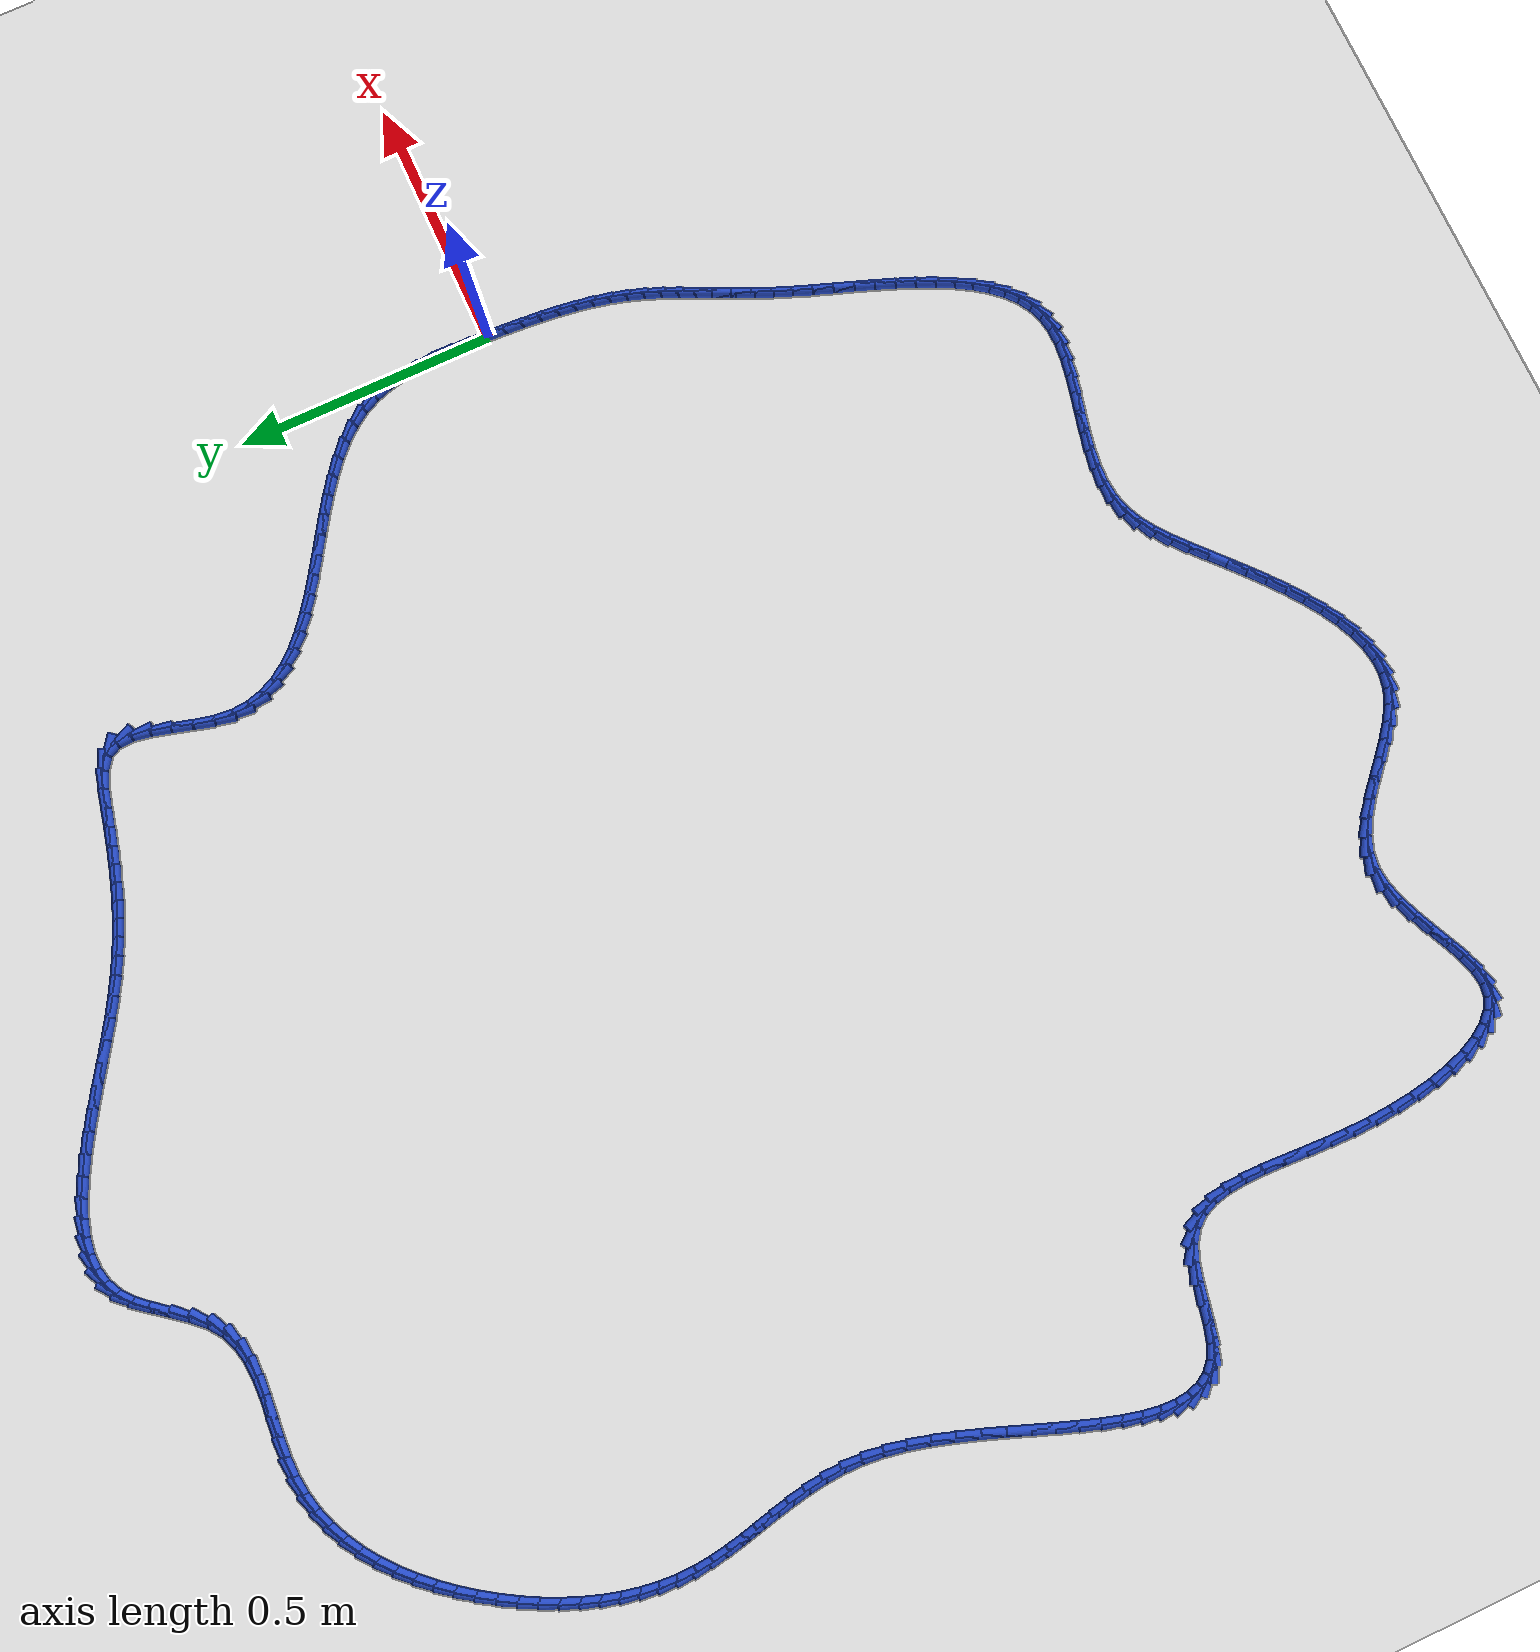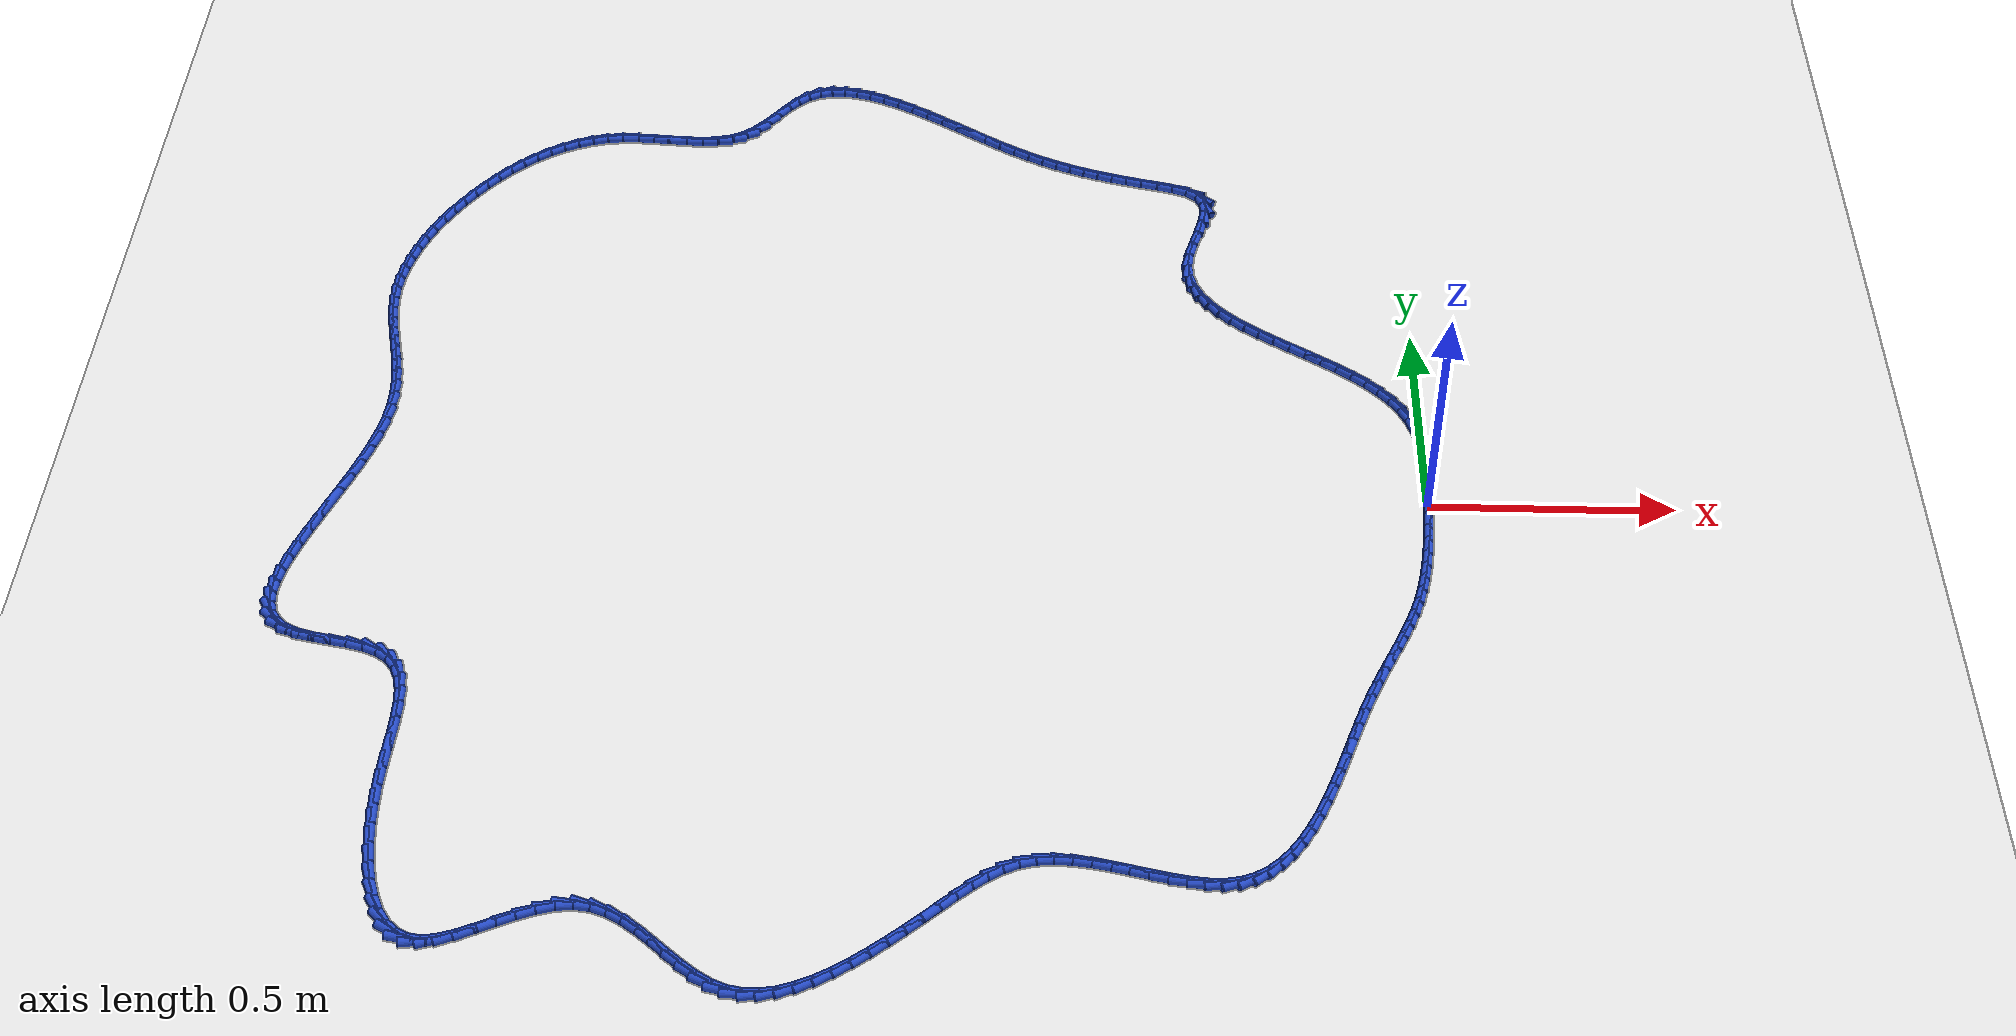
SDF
<sdf version="1.6">
 <world name="default">
  <light name="sun" type="directional">
   <pose>0 0 10 0 -0 0</pose>
   <diffuse>0.8 0.8 0.8 1</diffuse>
   <specular>0.2 0.2 0.2 1</specular>
   <attenuation>
    <range>1000</range>
    <constant>0.9</constant>
    <linear>0.01</linear>
    <quadratic>0.001</quadratic>
   </attenuation>
   <direction>-0.5 0.1 -0.9</direction>
  </light>
  <model name="ground_plane">
   <static>1</static>
   <link name="link">
    <collision name="collision">
     <geometry><plane><normal>0 0 1</normal><size>100 100</size></plane></geometry>
     <surface><friction><ode><mu>100</mu><mu2>50</mu2></ode></friction></surface>
    </collision>
    <visual name="visual">
     <cast_shadows>0</cast_shadows>
     <geometry><plane><normal>0 0 1</normal><size>100 100</size></plane></geometry>
     <material>
      <script><uri>file://media/materials/scripts/gazebo.material</uri><name>Gazebo/WhiteGlow</name></script>
     </material>
    </visual>
   </link>
  </model>
  <gravity>0 0 -9.8</gravity>
  <magnetic_field>6e-06 2.3e-05 -4.2e-05</magnetic_field>
  <atmosphere type="adiabatic"/>
  <physics name="default_physics" default="0" type="ode">
   <max_step_size>0.001</max_step_size>
   <real_time_factor>1</real_time_factor>
   <real_time_update_rate>1000</real_time_update_rate>
  </physics>
  <scene><ambient>0.4 0.4 0.4 1</ambient><background>0.7 0.7 0.7 1</background><shadows>1</shadows></scene>
  <spherical_coordinates>
   <surface_model>EARTH_WGS84</surface_model>
   <latitude_deg>0</latitude_deg>
   <longitude_deg>0</longitude_deg>
   <elevation>0</elevation>
   <heading_deg>0</heading_deg>
  </spherical_coordinates>
  <model name="line">
   <link name="link_0">
    <pose>7.15573433840433e-18 6.245004513516506e-17 0.01 0 1.57 1.526935981426265</pose>
    <collision name="collision">
     <geometry><cylinder><radius>0.01</radius><length>0.08</length></cylinder></geometry>
    </collision>
    <visual name="visual">
     <material>
      <script><name>Gazebo/Blue</name><uri>file://media/materials/scripts/gazebo.material</uri></script>
     </material>
     <geometry><cylinder><radius>0.01</radius><length>0.08</length></cylinder></geometry>
    </visual>
   </link>
   <link name="link_1">
    <pose>0.0015649802183906286 0.03565809943909584 0.01 0 1.57 1.547007990299336</pose>
    <collision name="collision">
     <geometry><cylinder><radius>0.01</radius><length>0.08</length></cylinder></geometry>
    </collision>
    <visual name="visual">
     <material>
      <script><name>Gazebo/Blue</name><uri>file://media/materials/scripts/gazebo.material</uri></script>
     </material>
     <geometry><cylinder><radius>0.01</radius><length>0.08</length></cylinder></geometry>
    </visual>
   </link>
   <link name="link_2">
    <pose>0.002413735943892878 0.07133085950181656 0.01 0 1.57 -1.5597450419062657</pose>
    <collision name="collision">
     <geometry><cylinder><radius>0.01</radius><length>0.08</length></cylinder></geometry>
    </collision>
    <visual name="visual">
     <material>
      <script><name>Gazebo/Blue</name><uri>file://media/materials/scripts/gazebo.material</uri></script>
     </material>
     <geometry><cylinder><radius>0.01</radius><length>0.08</length></cylinder></geometry>
    </visual>
   </link>
   <link name="link_3">
    <pose>0.0020225366100942973 0.10672795692253452 0.01 0 1.57 -1.5090084050465444</pose>
    <collision name="collision">
     <geometry><cylinder><radius>0.01</radius><length>0.08</length></cylinder></geometry>
    </collision>
    <visual name="visual">
     <material>
      <script><name>Gazebo/Blue</name><uri>file://media/materials/scripts/gazebo.material</uri></script>
     </material>
     <geometry><cylinder><radius>0.01</radius><length>0.08</length></cylinder></geometry>
    </visual>
   </link>
   <link name="link_4">
    <pose>-0.00013234834941757475 0.14155906843562185 0.01 0 1.57 -1.4407810871709563</pose>
    <collision name="collision">
     <geometry><cylinder><radius>0.01</radius><length>0.08</length></cylinder></geometry>
    </collision>
    <visual name="visual">
     <material>
      <script><name>Gazebo/Blue</name><uri>file://media/materials/scripts/gazebo.material</uri></script>
     </material>
     <geometry><cylinder><radius>0.01</radius><length>0.08</length></cylinder></geometry>
    </visual>
   </link>
   <link name="link_5">
    <pose>-0.004574649501055192 0.175533870775451 0.01 0 1.57 -1.3533382078417666</pose>
    <collision name="collision">
     <geometry><cylinder><radius>0.01</radius><length>0.08</length></cylinder></geometry>
    </collision>
    <visual name="visual">
     <material>
      <script><name>Gazebo/Blue</name><uri>file://media/materials/scripts/gazebo.material</uri></script>
     </material>
     <geometry><cylinder><radius>0.01</radius><length>0.08</length></cylinder></geometry>
    </visual>
   </link>
   <link name="link_6">
    <pose>-0.01182809741123102 0.20836204067639408 0.01 0 1.57 -1.2454780661886489</pose>
    <collision name="collision">
     <geometry><cylinder><radius>0.01</radius><length>0.08</length></cylinder></geometry>
    </collision>
    <visual name="visual">
     <material>
      <script><name>Gazebo/Blue</name><uri>file://media/materials/scripts/gazebo.material</uri></script>
     </material>
     <geometry><cylinder><radius>0.01</radius><length>0.08</length></cylinder></geometry>
    </visual>
   </link>
   <link name="link_7">
    <pose>-0.022416422646357508 0.2397532548728233 0.01 0 1.57 -1.1175864413855836</pose>
    <collision name="collision">
     <geometry><cylinder><radius>0.01</radius><length>0.08</length></cylinder></geometry>
    </collision>
    <visual name="visual">
     <material>
      <script><name>Gazebo/Blue</name><uri>file://media/materials/scripts/gazebo.material</uri></script>
     </material>
     <geometry><cylinder><radius>0.01</radius><length>0.08</length></cylinder></geometry>
    </visual>
   </link>
   <link name="link_8">
    <pose>-0.03686335577284712 0.269417190099111 0.01 0 1.57 -0.9787864145099151</pose>
    <collision name="collision">
     <geometry><cylinder><radius>0.01</radius><length>0.08</length></cylinder></geometry>
    </collision>
    <visual name="visual">
     <material>
      <script><name>Gazebo/Blue</name><uri>file://media/materials/scripts/gazebo.material</uri></script>
     </material>
     <geometry><cylinder><radius>0.01</radius><length>0.08</length></cylinder></geometry>
    </visual>
   </link>
   <link name="link_9">
    <pose>-0.05551379721671593 0.29715140356162123 0.01 0 1.57 -0.8578253520761805</pose>
    <collision name="collision">
     <geometry><cylinder><radius>0.01</radius><length>0.08</length></cylinder></geometry>
    </collision>
    <visual name="visual">
     <material>
      <script><name>Gazebo/Blue</name><uri>file://media/materials/scripts/gazebo.material</uri></script>
     </material>
     <geometry><cylinder><radius>0.01</radius><length>0.08</length></cylinder></geometry>
    </visual>
   </link>
   <link name="link_10">
    <pose>-0.07796836102066894 0.32311920870063654 0.01 0 1.57 -0.7613462970906467</pose>
    <collision name="collision">
     <geometry><cylinder><radius>0.01</radius><length>0.08</length></cylinder></geometry>
    </collision>
    <visual name="visual">
     <material>
      <script><name>Gazebo/Blue</name><uri>file://media/materials/scripts/gazebo.material</uri></script>
     </material>
     <geometry><cylinder><radius>0.01</radius><length>0.08</length></cylinder></geometry>
    </visual>
   </link>
   <link name="link_11">
    <pose>-0.103634057336789 0.3475790595253034 0.01 0 1.57 -0.6871896803333584</pose>
    <collision name="collision">
     <geometry><cylinder><radius>0.01</radius><length>0.08</length></cylinder></geometry>
    </collision>
    <visual name="visual">
     <material>
      <script><name>Gazebo/Blue</name><uri>file://media/materials/scripts/gazebo.material</uri></script>
     </material>
     <geometry><cylinder><radius>0.01</radius><length>0.08</length></cylinder></geometry>
    </visual>
   </link>
   <link name="link_12">
    <pose>-0.13191789588612848 0.3707894102565844 0.01 0 1.57 -0.6325924469153109</pose>
    <collision name="collision">
     <geometry><cylinder><radius>0.01</radius><length>0.08</length></cylinder></geometry>
    </collision>
    <visual name="visual">
     <material>
      <script><name>Gazebo/Blue</name><uri>file://media/materials/scripts/gazebo.material</uri></script>
     </material>
     <geometry><cylinder><radius>0.01</radius><length>0.08</length></cylinder></geometry>
    </visual>
   </link>
   <link name="link_13">
    <pose>-0.16222688638973973 0.39300871511544244 0.01 0 1.57 -0.5950781534837368</pose>
    <collision name="collision">
     <geometry><cylinder><radius>0.01</radius><length>0.08</length></cylinder></geometry>
    </collision>
    <visual name="visual">
     <material>
      <script><name>Gazebo/Blue</name><uri>file://media/materials/scripts/gazebo.material</uri></script>
     </material>
     <geometry><cylinder><radius>0.01</radius><length>0.08</length></cylinder></geometry>
    </visual>
   </link>
   <link name="link_14">
    <pose>-0.19396803856867534 0.41449542832284053 0.01 0 1.57 -0.572814684261864</pose>
    <collision name="collision">
     <geometry><cylinder><radius>0.01</radius><length>0.08</length></cylinder></geometry>
    </collision>
    <visual name="visual">
     <material>
      <script><name>Gazebo/Blue</name><uri>file://media/materials/scripts/gazebo.material</uri></script>
     </material>
     <geometry><cylinder><radius>0.01</radius><length>0.08</length></cylinder></geometry>
    </visual>
   </link>
   <link name="link_15">
    <pose>-0.2265483621439877 0.43550800409974133 0.01 0 1.57 -0.5647166380640539</pose>
    <collision name="collision">
     <geometry><cylinder><radius>0.01</radius><length>0.08</length></cylinder></geometry>
    </collision>
    <visual name="visual">
     <material>
      <script><name>Gazebo/Blue</name><uri>file://media/materials/scripts/gazebo.material</uri></script>
     </material>
     <geometry><cylinder><radius>0.01</radius><length>0.08</length></cylinder></geometry>
    </visual>
   </link>
   <link name="link_16">
    <pose>-0.2593748668367293 0.4563048966671078 0.01 0 1.57 -0.5704625095506994</pose>
    <collision name="collision">
     <geometry><cylinder><radius>0.01</radius><length>0.08</length></cylinder></geometry>
    </collision>
    <visual name="visual">
     <material>
      <script><name>Gazebo/Blue</name><uri>file://media/materials/scripts/gazebo.material</uri></script>
     </material>
     <geometry><cylinder><radius>0.01</radius><length>0.08</length></cylinder></geometry>
    </visual>
   </link>
   <link name="link_17">
    <pose>-0.29185456236795254 0.47714456024590235 0.01 0 1.57 -0.5905071314055473</pose>
    <collision name="collision">
     <geometry><cylinder><radius>0.01</radius><length>0.08</length></cylinder></geometry>
    </collision>
    <visual name="visual">
     <material>
      <script><name>Gazebo/Blue</name><uri>file://media/materials/scripts/gazebo.material</uri></script>
     </material>
     <geometry><cylinder><radius>0.01</radius><length>0.08</length></cylinder></geometry>
    </visual>
   </link>
   <link name="link_18">
    <pose>-0.32339445845870973 0.4982854490570881 0.01 0 1.57 -0.6261148427597982</pose>
    <collision name="collision">
     <geometry><cylinder><radius>0.01</radius><length>0.08</length></cylinder></geometry>
    </collision>
    <visual name="visual">
     <material>
      <script><name>Gazebo/Blue</name><uri>file://media/materials/scripts/gazebo.material</uri></script>
     </material>
     <geometry><cylinder><radius>0.01</radius><length>0.08</length></cylinder></geometry>
    </visual>
   </link>
   <link name="link_19">
    <pose>-0.3534015648300535 0.5199860173216279 0.01 0 1.57 -0.6793957695988381</pose>
    <collision name="collision">
     <geometry><cylinder><radius>0.01</radius><length>0.08</length></cylinder></geometry>
    </collision>
    <visual name="visual">
     <material>
      <script><name>Gazebo/Blue</name><uri>file://media/materials/scripts/gazebo.material</uri></script>
     </material>
     <geometry><cylinder><radius>0.01</radius><length>0.08</length></cylinder></geometry>
    </visual>
   </link>
   <link name="link_20">
    <pose>-0.3812828912030363 0.5425047192604844 0.01 0 1.57 -0.7532653489869112</pose>
    <collision name="collision">
     <geometry><cylinder><radius>0.01</radius><length>0.08</length></cylinder></geometry>
    </collision>
    <visual name="visual">
     <material>
      <script><name>Gazebo/Blue</name><uri>file://media/materials/scripts/gazebo.material</uri></script>
     </material>
     <geometry><cylinder><radius>0.01</radius><length>0.08</length></cylinder></geometry>
    </visual>
   </link>
   <link name="link_21">
    <pose>-0.40644544729871046 0.5661000090946204 0.01 0 1.57 -0.8511319285466248</pose>
    <collision name="collision">
     <geometry><cylinder><radius>0.01</radius><length>0.08</length></cylinder></geometry>
    </collision>
    <visual name="visual">
     <material>
      <script><name>Gazebo/Blue</name><uri>file://media/materials/scripts/gazebo.material</uri></script>
     </material>
     <geometry><cylinder><radius>0.01</radius><length>0.08</length></cylinder></geometry>
    </visual>
   </link>
   <link name="link_22">
    <pose>-0.4282962428381285 0.5910303410449991 0.01 0 1.57 -0.9759477097483894</pose>
    <collision name="collision">
     <geometry><cylinder><radius>0.01</radius><length>0.08</length></cylinder></geometry>
    </collision>
    <visual name="visual">
     <material>
      <script><name>Gazebo/Blue</name><uri>file://media/materials/scripts/gazebo.material</uri></script>
     </material>
     <geometry><cylinder><radius>0.01</radius><length>0.08</length></cylinder></geometry>
    </visual>
   </link>
   <link name="link_23">
    <pose>-0.44624228754234285 0.6175541693325827 0.01 0 1.57 -1.1282164633529859</pose>
    <collision name="collision">
     <geometry><cylinder><radius>0.01</radius><length>0.08</length></cylinder></geometry>
    </collision>
    <visual name="visual">
     <material>
      <script><name>Gazebo/Blue</name><uri>file://media/materials/scripts/gazebo.material</uri></script>
     </material>
     <geometry><cylinder><radius>0.01</radius><length>0.08</length></cylinder></geometry>
    </visual>
   </link>
   <link name="link_24">
    <pose>-0.4596905911324059 0.6459299481783345 0.01 0 1.57 -1.30322708645775</pose>
    <collision name="collision">
     <geometry><cylinder><radius>0.01</radius><length>0.08</length></cylinder></geometry>
    </collision>
    <visual name="visual">
     <material>
      <script><name>Gazebo/Blue</name><uri>file://media/materials/scripts/gazebo.material</uri></script>
     </material>
     <geometry><cylinder><radius>0.01</radius><length>0.08</length></cylinder></geometry>
    </visual>
   </link>
   <link name="link_25">
    <pose>-0.46804816332937044 0.6764161318032174 0.01 0 1.57 -1.4895920281579804</pose>
    <collision name="collision">
     <geometry><cylinder><radius>0.01</radius><length>0.08</length></cylinder></geometry>
    </collision>
    <visual name="visual">
     <material>
      <script><name>Gazebo/Blue</name><uri>file://media/materials/scripts/gazebo.material</uri></script>
     </material>
     <geometry><cylinder><radius>0.01</radius><length>0.08</length></cylinder></geometry>
    </visual>
   </link>
   <link name="link_26">
    <pose>-0.47072201385428825 0.7092711744281934 0.01 0 1.57 1.4707584314168691</pose>
    <collision name="collision">
     <geometry><cylinder><radius>0.01</radius><length>0.08</length></cylinder></geometry>
    </collision>
    <visual name="visual">
     <material>
      <script><name>Gazebo/Blue</name><uri>file://media/materials/scripts/gazebo.material</uri></script>
     </material>
     <geometry><cylinder><radius>0.01</radius><length>0.08</length></cylinder></geometry>
    </visual>
   </link>
   <link name="link_27">
    <pose>-0.46716271543037835 0.7447319081786529 0.01 0 1.57 1.341338182621031</pose>
    <collision name="collision">
     <geometry><cylinder><radius>0.01</radius><length>0.08</length></cylinder></geometry>
    </collision>
    <visual name="visual">
     <material>
      <script><name>Gazebo/Blue</name><uri>file://media/materials/scripts/gazebo.material</uri></script>
     </material>
     <geometry><cylinder><radius>0.01</radius><length>0.08</length></cylinder></geometry>
    </visual>
   </link>
   <link name="link_28">
    <pose>-0.4583991243492406 0.7822517986427662 0.01 0 1.57 1.2904919899445115</pose>
    <collision name="collision">
     <geometry><cylinder><radius>0.01</radius><length>0.08</length></cylinder></geometry>
    </collision>
    <visual name="visual">
     <material>
      <script><name>Gazebo/Blue</name><uri>file://media/materials/scripts/gazebo.material</uri></script>
     </material>
     <geometry><cylinder><radius>0.01</radius><length>0.08</length></cylinder></geometry>
    </visual>
   </link>
   <link name="link_29">
    <pose>-0.4474460662436757 0.8202985937867253 0.01 0 1.57 1.306655985645283</pose>
    <collision name="collision">
     <geometry><cylinder><radius>0.01</radius><length>0.08</length></cylinder></geometry>
    </collision>
    <visual name="visual">
     <material>
      <script><name>Gazebo/Blue</name><uri>file://media/materials/scripts/gazebo.material</uri></script>
     </material>
     <geometry><cylinder><radius>0.01</radius><length>0.08</length></cylinder></geometry>
    </visual>
   </link>
   <link name="link_30">
    <pose>-0.437444818693914 0.8572772783153101 0.01 0 1.57 1.4002964739328356</pose>
    <collision name="collision">
     <geometry><cylinder><radius>0.01</radius><length>0.08</length></cylinder></geometry>
    </collision>
    <visual name="visual">
     <material>
      <script><name>Gazebo/Blue</name><uri>file://media/materials/scripts/gazebo.material</uri></script>
     </material>
     <geometry><cylinder><radius>0.01</radius><length>0.08</length></cylinder></geometry>
    </visual>
   </link>
   <link name="link_31">
    <pose>-0.4315366592801862 0.8915928369333002 0.01 0 1.57 -1.526702495522563</pose>
    <collision name="collision">
     <geometry><cylinder><radius>0.01</radius><length>0.08</length></cylinder></geometry>
    </collision>
    <visual name="visual">
     <material>
      <script><name>Gazebo/Blue</name><uri>file://media/materials/scripts/gazebo.material</uri></script>
     </material>
     <geometry><cylinder><radius>0.01</radius><length>0.08</length></cylinder></geometry>
    </visual>
   </link>
   <link name="link_32">
    <pose>-0.43286286558272274 0.9216502543454757 0.01 0 1.57 -1.1204673625346468</pose>
    <collision name="collision">
     <geometry><cylinder><radius>0.01</radius><length>0.08</length></cylinder></geometry>
    </collision>
    <visual name="visual">
     <material>
      <script><name>Gazebo/Blue</name><uri>file://media/materials/scripts/gazebo.material</uri></script>
     </material>
     <geometry><cylinder><radius>0.01</radius><length>0.08</length></cylinder></geometry>
    </visual>
   </link>
   <link name="link_33">
    <pose>-0.4445646853662194 0.9458545299295772 0.01 0 1.57 -0.6320719578579088</pose>
    <collision name="collision">
     <geometry><cylinder><radius>0.01</radius><length>0.08</length></cylinder></geometry>
    </collision>
    <visual name="visual">
     <material>
      <script><name>Gazebo/Blue</name><uri>file://media/materials/scripts/gazebo.material</uri></script>
     </material>
     <geometry><cylinder><radius>0.01</radius><length>0.08</length></cylinder></geometry>
    </visual>
   </link>
   <link name="link_34">
    <pose>-0.4683856982567521 0.9632984900398741 0.01 0 1.57 -0.3613437334460103</pose>
    <collision name="collision">
     <geometry><cylinder><radius>0.01</radius><length>0.08</length></cylinder></geometry>
    </collision>
    <visual name="visual">
     <material>
      <script><name>Gazebo/Blue</name><uri>file://media/materials/scripts/gazebo.material</uri></script>
     </material>
     <geometry><cylinder><radius>0.01</radius><length>0.08</length></cylinder></geometry>
    </visual>
   </link>
   <link name="link_35">
    <pose>-0.5009369166591825 0.9756008239991414 0.01 0 1.57 -0.24959799395603197</pose>
    <collision name="collision">
     <geometry><cylinder><radius>0.01</radius><length>0.08</length></cylinder></geometry>
    </collision>
    <visual name="visual">
     <material>
      <script><name>Gazebo/Blue</name><uri>file://media/materials/scripts/gazebo.material</uri></script>
     </material>
     <geometry><cylinder><radius>0.01</radius><length>0.08</length></cylinder></geometry>
    </visual>
   </link>
   <link name="link_36">
    <pose>-0.5376514940819966 0.9849598745550893 0.01 0 1.57 -0.2292153591801549</pose>
    <collision name="collision">
     <geometry><cylinder><radius>0.01</radius><length>0.08</length></cylinder></geometry>
    </collision>
    <visual name="visual">
     <material>
      <script><name>Gazebo/Blue</name><uri>file://media/materials/scripts/gazebo.material</uri></script>
     </material>
     <geometry><cylinder><radius>0.01</radius><length>0.08</length></cylinder></geometry>
    </visual>
   </link>
   <link name="link_37">
    <pose>-0.5741827053642955 0.9934831854203502 0.01 0 1.57 -0.24431994710885363</pose>
    <collision name="collision">
     <geometry><cylinder><radius>0.01</radius><length>0.08</length></cylinder></geometry>
    </collision>
    <visual name="visual">
     <material>
      <script><name>Gazebo/Blue</name><uri>file://media/materials/scripts/gazebo.material</uri></script>
     </material>
     <geometry><cylinder><radius>0.01</radius><length>0.08</length></cylinder></geometry>
    </visual>
   </link>
   <link name="link_38">
    <pose>-0.6089297309856214 1.0021456268775741 0.01 0 1.57 -0.26472490879722876</pose>
    <collision name="collision">
     <geometry><cylinder><radius>0.01</radius><length>0.08</length></cylinder></geometry>
    </collision>
    <visual name="visual">
     <material>
      <script><name>Gazebo/Blue</name><uri>file://media/materials/scripts/gazebo.material</uri></script>
     </material>
     <geometry><cylinder><radius>0.01</radius><length>0.08</length></cylinder></geometry>
    </visual>
   </link>
   <link name="link_39">
    <pose>-0.6421563383784145 1.0111529356789852 0.01 0 1.57 -0.2897821033669454</pose>
    <collision name="collision">
     <geometry><cylinder><radius>0.01</radius><length>0.08</length></cylinder></geometry>
    </collision>
    <visual name="visual">
     <material>
      <script><name>Gazebo/Blue</name><uri>file://media/materials/scripts/gazebo.material</uri></script>
     </material>
     <geometry><cylinder><radius>0.01</radius><length>0.08</length></cylinder></geometry>
    </visual>
   </link>
   <link name="link_40">
    <pose>-0.6741618318921627 1.0206961897621964 0.01 0 1.57 -0.3191148517211513</pose>
    <collision name="collision">
     <geometry><cylinder><radius>0.01</radius><length>0.08</length></cylinder></geometry>
    </collision>
    <visual name="visual">
     <material>
      <script><name>Gazebo/Blue</name><uri>file://media/materials/scripts/gazebo.material</uri></script>
     </material>
     <geometry><cylinder><radius>0.01</radius><length>0.08</length></cylinder></geometry>
    </visual>
   </link>
   <link name="link_41">
    <pose>-0.7052455158763539 1.0309664670648213 0.01 0 1.57 -0.3520025938738875</pose>
    <collision name="collision">
     <geometry><cylinder><radius>0.01</radius><length>0.08</length></cylinder></geometry>
    </collision>
    <visual name="visual">
     <material>
      <script><name>Gazebo/Blue</name><uri>file://media/materials/scripts/gazebo.material</uri></script>
     </material>
     <geometry><cylinder><radius>0.01</radius><length>0.08</length></cylinder></geometry>
    </visual>
   </link>
   <link name="link_42">
    <pose>-0.735706694680476 1.0421548455244727 0.01 0 1.57 -0.3874197609356239</pose>
    <collision name="collision">
     <geometry><cylinder><radius>0.01</radius><length>0.08</length></cylinder></geometry>
    </collision>
    <visual name="visual">
     <material>
      <script><name>Gazebo/Blue</name><uri>file://media/materials/scripts/gazebo.material</uri></script>
     </material>
     <geometry><cylinder><radius>0.01</radius><length>0.08</length></cylinder></geometry>
    </visual>
   </link>
   <link name="link_43">
    <pose>-0.765844672654017 1.054452403078764 0.01 0 1.57 -0.4241366729015961</pose>
    <collision name="collision">
     <geometry><cylinder><radius>0.01</radius><length>0.08</length></cylinder></geometry>
    </collision>
    <visual name="visual">
     <material>
      <script><name>Gazebo/Blue</name><uri>file://media/materials/scripts/gazebo.material</uri></script>
     </material>
     <geometry><cylinder><radius>0.01</radius><length>0.08</length></cylinder></geometry>
    </visual>
   </link>
   <link name="link_44">
    <pose>-0.7959587541464647 1.068050217665308 0.01 0 1.57 -0.4608639670771905</pose>
    <collision name="collision">
     <geometry><cylinder><radius>0.01</radius><length>0.08</length></cylinder></geometry>
    </collision>
    <visual name="visual">
     <material>
      <script><name>Gazebo/Blue</name><uri>file://media/materials/scripts/gazebo.material</uri></script>
     </material>
     <geometry><cylinder><radius>0.01</radius><length>0.08</length></cylinder></geometry>
    </visual>
   </link>
   <link name="link_45">
    <pose>-0.8263482435073073 1.0831393672217182 0.01 0 1.57 -0.49640494035453653</pose>
    <collision name="collision">
     <geometry><cylinder><radius>0.01</radius><length>0.08</length></cylinder></geometry>
    </collision>
    <visual name="visual">
     <material>
      <script><name>Gazebo/Blue</name><uri>file://media/materials/scripts/gazebo.material</uri></script>
     </material>
     <geometry><cylinder><radius>0.01</radius><length>0.08</length></cylinder></geometry>
    </visual>
   </link>
   <link name="link_46">
    <pose>-0.8573124450860327 1.0999109296856076 0.01 0 1.57 -0.5297279434090891</pose>
    <collision name="collision">
     <geometry><cylinder><radius>0.01</radius><length>0.08</length></cylinder></geometry>
    </collision>
    <visual name="visual">
     <material>
      <script><name>Gazebo/Blue</name><uri>file://media/materials/scripts/gazebo.material</uri></script>
     </material>
     <geometry><cylinder><radius>0.01</radius><length>0.08</length></cylinder></geometry>
    </visual>
   </link>
   <link name="link_47">
    <pose>-0.8891484954340187 1.1185525804634986 0.01 0 1.57 -0.5564569329561805</pose>
    <collision name="collision">
     <geometry><cylinder><radius>0.01</radius><length>0.08</length></cylinder></geometry>
    </collision>
    <visual name="visual">
     <material>
      <script><name>Gazebo/Blue</name><uri>file://media/materials/scripts/gazebo.material</uri></script>
     </material>
     <geometry><cylinder><radius>0.01</radius><length>0.08</length></cylinder></geometry>
    </visual>
   </link>
   <link name="link_48">
    <pose>-0.9219746853256074 1.138971282328219 0.01 0 1.57 -0.571351419566026</pose>
    <collision name="collision">
     <geometry><cylinder><radius>0.01</radius><length>0.08</length></cylinder></geometry>
    </collision>
    <visual name="visual">
     <material>
      <script><name>Gazebo/Blue</name><uri>file://media/materials/scripts/gazebo.material</uri></script>
     </material>
     <geometry><cylinder><radius>0.01</radius><length>0.08</length></cylinder></geometry>
    </visual>
   </link>
   <link name="link_49">
    <pose>-0.9555996762825264 1.1605880103798027 0.01 0 1.57 -0.5754763204242745</pose>
    <collision name="collision">
     <geometry><cylinder><radius>0.01</radius><length>0.08</length></cylinder></geometry>
    </collision>
    <visual name="visual">
     <material>
      <script><name>Gazebo/Blue</name><uri>file://media/materials/scripts/gazebo.material</uri></script>
     </material>
     <geometry><cylinder><radius>0.01</radius><length>0.08</length></cylinder></geometry>
    </visual>
   </link>
   <link name="link_50">
    <pose>-0.9898013090590866 1.18277536407902 0.01 0 1.57 -0.5696141984370579</pose>
    <collision name="collision">
     <geometry><cylinder><radius>0.01</radius><length>0.08</length></cylinder></geometry>
    </collision>
    <visual name="visual">
     <material>
      <script><name>Gazebo/Blue</name><uri>file://media/materials/scripts/gazebo.material</uri></script>
     </material>
     <geometry><cylinder><radius>0.01</radius><length>0.08</length></cylinder></geometry>
    </visual>
   </link>
   <link name="link_51">
    <pose>-1.0243574244095994 1.20490594288664 0.01 0 1.57 -0.5537364106939168</pose>
    <collision name="collision">
     <geometry><cylinder><radius>0.01</radius><length>0.08</length></cylinder></geometry>
    </collision>
    <visual name="visual">
     <material>
      <script><name>Gazebo/Blue</name><uri>file://media/materials/scripts/gazebo.material</uri></script>
     </material>
     <geometry><cylinder><radius>0.01</radius><length>0.08</length></cylinder></geometry>
    </visual>
   </link>
   <link name="link_52">
    <pose>-1.0590458630883752 1.2263523462634318 0.01 0 1.57 -0.5270453845238067</pose>
    <collision name="collision">
     <geometry><cylinder><radius>0.01</radius><length>0.08</length></cylinder></geometry>
    </collision>
    <visual name="visual">
     <material>
      <script><name>Gazebo/Blue</name><uri>file://media/materials/scripts/gazebo.material</uri></script>
     </material>
     <geometry><cylinder><radius>0.01</radius><length>0.08</length></cylinder></geometry>
    </visual>
   </link>
   <link name="link_53">
    <pose>-1.0936444658497246 1.2464871736701642 0.01 0 1.57 -0.4879037341892201</pose>
    <collision name="collision">
     <geometry><cylinder><radius>0.01</radius><length>0.08</length></cylinder></geometry>
    </collision>
    <visual name="visual">
     <material>
      <script><name>Gazebo/Blue</name><uri>file://media/materials/scripts/gazebo.material</uri></script>
     </material>
     <geometry><cylinder><radius>0.01</radius><length>0.08</length></cylinder></geometry>
    </visual>
   </link>
   <link name="link_54">
    <pose>-1.1279310734479593 1.2646830245676064 0.01 0 1.57 -0.43366292454285515</pose>
    <collision name="collision">
     <geometry><cylinder><radius>0.01</radius><length>0.08</length></cylinder></geometry>
    </collision>
    <visual name="visual">
     <material>
      <script><name>Gazebo/Blue</name><uri>file://media/materials/scripts/gazebo.material</uri></script>
     </material>
     <geometry><cylinder><radius>0.01</radius><length>0.08</length></cylinder></geometry>
    </visual>
   </link>
   <link name="link_55">
    <pose>-1.1616835266373888 1.2803124984165275 0.01 0 1.57 -0.36042082061415953</pose>
    <collision name="collision">
     <geometry><cylinder><radius>0.01</radius><length>0.08</length></cylinder></geometry>
    </collision>
    <visual name="visual">
     <material>
      <script><name>Gazebo/Blue</name><uri>file://media/materials/scripts/gazebo.material</uri></script>
     </material>
     <geometry><cylinder><radius>0.01</radius><length>0.08</length></cylinder></geometry>
    </visual>
   </link>
   <link name="link_56">
    <pose>-1.194679666172325 1.2927481946776969 0.01 0 1.57 -0.26283097569274455</pose>
    <collision name="collision">
     <geometry><cylinder><radius>0.01</radius><length>0.08</length></cylinder></geometry>
    </collision>
    <visual name="visual">
     <material>
      <script><name>Gazebo/Blue</name><uri>file://media/materials/scripts/gazebo.material</uri></script>
     </material>
     <geometry><cylinder><radius>0.01</radius><length>0.08</length></cylinder></geometry>
    </visual>
   </link>
   <link name="link_57">
    <pose>-1.2266973328070785 1.3013627128118834 0.01 0 1.57 -0.1343684575006586</pose>
    <collision name="collision">
     <geometry><cylinder><radius>0.01</radius><length>0.08</length></cylinder></geometry>
    </collision>
    <visual name="visual">
     <material>
      <script><name>Gazebo/Blue</name><uri>file://media/materials/scripts/gazebo.material</uri></script>
     </material>
     <geometry><cylinder><radius>0.01</radius><length>0.08</length></cylinder></geometry>
    </visual>
   </link>
   <link name="link_58">
    <pose>-1.25751436729596 1.3055286522798564 0.01 0 1.57 0.030949908836466963</pose>
    <collision name="collision">
     <geometry><cylinder><radius>0.01</radius><length>0.08</length></cylinder></geometry>
    </collision>
    <visual name="visual">
     <material>
      <script><name>Gazebo/Blue</name><uri>file://media/materials/scripts/gazebo.material</uri></script>
     </material>
     <geometry><cylinder><radius>0.01</radius><length>0.08</length></cylinder></geometry>
    </visual>
   </link>
   <link name="link_59">
    <pose>-1.2869086103932803 1.3046186125423849 0.01 0 1.57 0.23396297029799276</pose>
    <collision name="collision">
     <geometry><cylinder><radius>0.01</radius><length>0.08</length></cylinder></geometry>
    </collision>
    <visual name="visual">
     <material>
      <script><name>Gazebo/Blue</name><uri>file://media/materials/scripts/gazebo.material</uri></script>
     </material>
     <geometry><cylinder><radius>0.01</radius><length>0.08</length></cylinder></geometry>
    </visual>
   </link>
   <link name="link_60">
    <pose>-1.31465790285335 1.2980051930602379 0.01 0 1.57 0.4637436852306395</pose>
    <collision name="collision">
     <geometry><cylinder><radius>0.01</radius><length>0.08</length></cylinder></geometry>
    </collision>
    <visual name="visual">
     <material>
      <script><name>Gazebo/Blue</name><uri>file://media/materials/scripts/gazebo.material</uri></script>
     </material>
     <geometry><cylinder><radius>0.01</radius><length>0.08</length></cylinder></geometry>
    </visual>
   </link>
   <link name="link_61">
    <pose>-1.3405400854304812 1.285060993294185 0.01 0 1.57 0.6919482767564125</pose>
    <collision name="collision">
     <geometry><cylinder><radius>0.01</radius><length>0.08</length></cylinder></geometry>
    </collision>
    <visual name="visual">
     <material>
      <script><name>Gazebo/Blue</name><uri>file://media/materials/scripts/gazebo.material</uri></script>
     </material>
     <geometry><cylinder><radius>0.01</radius><length>0.08</length></cylinder></geometry>
    </visual>
   </link>
   <link name="link_62">
    <pose>-1.364384814122442 1.2653028507944972 0.01 0 1.57 0.8456184677379267</pose>
    <collision name="collision">
     <geometry><cylinder><radius>0.01</radius><length>0.08</length></cylinder></geometry>
    </collision>
    <visual name="visual">
     <material>
      <script><name>Gazebo/Blue</name><uri>file://media/materials/scripts/gazebo.material</uri></script>
     </material>
     <geometry><cylinder><radius>0.01</radius><length>0.08</length></cylinder></geometry>
    </visual>
   </link>
   <link name="link_63">
    <pose>-1.3866970454421277 1.2401274371069797 0.01 0 1.57 0.9081050745069981</pose>
    <collision name="collision">
     <geometry><cylinder><radius>0.01</radius><length>0.08</length></cylinder></geometry>
    </collision>
    <visual name="visual">
     <material>
      <script><name>Gazebo/Blue</name><uri>file://media/materials/scripts/gazebo.material</uri></script>
     </material>
     <geometry><cylinder><radius>0.01</radius><length>0.08</length></cylinder></geometry>
    </visual>
   </link>
   <link name="link_64">
    <pose>-1.4084547564450534 1.21224817102802 0.01 0 1.57 0.8978789376927718</pose>
    <collision name="collision">
     <geometry><cylinder><radius>0.01</radius><length>0.08</length></cylinder></geometry>
    </collision>
    <visual name="visual">
     <material>
      <script><name>Gazebo/Blue</name><uri>file://media/materials/scripts/gazebo.material</uri></script>
     </material>
     <geometry><cylinder><radius>0.01</radius><length>0.08</length></cylinder></geometry>
    </visual>
   </link>
   <link name="link_65">
    <pose>-1.4306456691011544 1.1844055982715758 0.01 0 1.57 0.8152492349469489</pose>
    <collision name="collision">
     <geometry><cylinder><radius>0.01</radius><length>0.08</length></cylinder></geometry>
    </collision>
    <visual name="visual">
     <material>
      <script><name>Gazebo/Blue</name><uri>file://media/materials/scripts/gazebo.material</uri></script>
     </material>
     <geometry><cylinder><radius>0.01</radius><length>0.08</length></cylinder></geometry>
    </visual>
   </link>
   <link name="link_66">
    <pose>-1.4542575053803661 1.159340264551606 0.01 0 1.57 0.6445946274945872</pose>
    <collision name="collision">
     <geometry><cylinder><radius>0.01</radius><length>0.08</length></cylinder></geometry>
    </collision>
    <visual name="visual">
     <material>
      <script><name>Gazebo/Blue</name><uri>file://media/materials/scripts/gazebo.material</uri></script>
     </material>
     <geometry><cylinder><radius>0.01</radius><length>0.08</length></cylinder></geometry>
    </visual>
   </link>
   <link name="link_67">
    <pose>-1.480274461597035 1.139783057714631 0.01 0 1.57 0.41050073762384276</pose>
    <collision name="collision">
     <geometry><cylinder><radius>0.01</radius><length>0.08</length></cylinder></geometry>
    </collision>
    <visual name="visual">
     <material>
      <script><name>Gazebo/Blue</name><uri>file://media/materials/scripts/gazebo.material</uri></script>
     </material>
     <geometry><cylinder><radius>0.01</radius><length>0.08</length></cylinder></geometry>
    </visual>
   </link>
   <link name="link_68">
    <pose>-1.5092144609077178 1.1271875983773147 0.01 0 1.57 0.21052976203073154</pose>
    <collision name="collision">
     <geometry><cylinder><radius>0.01</radius><length>0.08</length></cylinder></geometry>
    </collision>
    <visual name="visual">
     <material>
      <script><name>Gazebo/Blue</name><uri>file://media/materials/scripts/gazebo.material</uri></script>
     </material>
     <geometry><cylinder><radius>0.01</radius><length>0.08</length></cylinder></geometry>
    </visual>
   </link>
   <link name="link_69">
    <pose>-1.5406676934555041 1.1204661578284247 0.01 0 1.57 0.06674664311860688</pose>
    <collision name="collision">
     <geometry><cylinder><radius>0.01</radius><length>0.08</length></cylinder></geometry>
    </collision>
    <visual name="visual">
     <material>
      <script><name>Gazebo/Blue</name><uri>file://media/materials/scripts/gazebo.material</uri></script>
     </material>
     <geometry><cylinder><radius>0.01</radius><length>0.08</length></cylinder></geometry>
    </visual>
   </link>
   <link name="link_70">
    <pose>-1.574114599365697 1.118230367916409 0.01 0 1.57 -0.02466474017385754</pose>
    <collision name="collision">
     <geometry><cylinder><radius>0.01</radius><length>0.08</length></cylinder></geometry>
    </collision>
    <visual name="visual">
     <material>
      <script><name>Gazebo/Blue</name><uri>file://media/materials/scripts/gazebo.material</uri></script>
     </material>
     <geometry><cylinder><radius>0.01</radius><length>0.08</length></cylinder></geometry>
    </visual>
   </link>
   <link name="link_71">
    <pose>-1.6090356187635986 1.1190918604897155 0.01 0 1.57 -0.07152560560320889</pose>
    <collision name="collision">
     <geometry><cylinder><radius>0.01</radius><length>0.08</length></cylinder></geometry>
    </collision>
    <visual name="visual">
     <material>
      <script><name>Gazebo/Blue</name><uri>file://media/materials/scripts/gazebo.material</uri></script>
     </material>
     <geometry><cylinder><radius>0.01</radius><length>0.08</length></cylinder></geometry>
    </visual>
   </link>
   <link name="link_72">
    <pose>-1.6449111917745138 1.121662267396793 0.01 0 1.57 -0.07944981194883555</pose>
    <collision name="collision">
     <geometry><cylinder><radius>0.01</radius><length>0.08</length></cylinder></geometry>
    </collision>
    <visual name="visual">
     <material>
      <script><name>Gazebo/Blue</name><uri>file://media/materials/scripts/gazebo.material</uri></script>
     </material>
     <geometry><cylinder><radius>0.01</radius><length>0.08</length></cylinder></geometry>
    </visual>
   </link>
   <link name="link_73">
    <pose>-1.681221758523744 1.1245532204860886 0.01 0 1.57 -0.05028416706044684</pose>
    <collision name="collision">
     <geometry><cylinder><radius>0.01</radius><length>0.08</length></cylinder></geometry>
    </collision>
    <visual name="visual">
     <material>
      <script><name>Gazebo/Blue</name><uri>file://media/materials/scripts/gazebo.material</uri></script>
     </material>
     <geometry><cylinder><radius>0.01</radius><length>0.08</length></cylinder></geometry>
    </visual>
   </link>
   <link name="link_74">
    <pose>-1.7174477591365935 1.1263763516060512 0.01 0 1.57 0.017769765742580667</pose>
    <collision name="collision">
     <geometry><cylinder><radius>0.01</radius><length>0.08</length></cylinder></geometry>
    </collision>
    <visual name="visual">
     <material>
      <script><name>Gazebo/Blue</name><uri>file://media/materials/scripts/gazebo.material</uri></script>
     </material>
     <geometry><cylinder><radius>0.01</radius><length>0.08</length></cylinder></geometry>
    </visual>
   </link>
   <link name="link_75">
    <pose>-1.7530696337383647 1.125743292605128 0.01 0 1.57 0.1236331047392959</pose>
    <collision name="collision">
     <geometry><cylinder><radius>0.01</radius><length>0.08</length></cylinder></geometry>
    </collision>
    <visual name="visual">
     <material>
      <script><name>Gazebo/Blue</name><uri>file://media/materials/scripts/gazebo.material</uri></script>
     </material>
     <geometry><cylinder><radius>0.01</radius><length>0.08</length></cylinder></geometry>
    </visual>
   </link>
   <link name="link_76">
    <pose>-1.7876226589201585 1.121449495394555 0.01 0 1.57 0.23743610870200488</pose>
    <collision name="collision">
     <geometry><cylinder><radius>0.01</radius><length>0.08</length></cylinder></geometry>
    </collision>
    <visual name="visual">
     <material>
      <script><name>Gazebo/Blue</name><uri>file://media/materials/scripts/gazebo.material</uri></script>
     </material>
     <geometry><cylinder><radius>0.01</radius><length>0.08</length></cylinder></geometry>
    </visual>
   </link>
   <link name="link_77">
    <pose>-1.8209671794406903 1.1133800891671355 0.01 0 1.57 0.3455067567355999</pose>
    <collision name="collision">
     <geometry><cylinder><radius>0.01</radius><length>0.08</length></cylinder></geometry>
    </collision>
    <visual name="visual">
     <material>
      <script><name>Gazebo/Blue</name><uri>file://media/materials/scripts/gazebo.material</uri></script>
     </material>
     <geometry><cylinder><radius>0.01</radius><length>0.08</length></cylinder></geometry>
    </visual>
   </link>
   <link name="link_78">
    <pose>-1.85308286913078 1.1018202120733536 0.01 0 1.57 0.44616504954066794</pose>
    <collision name="collision">
     <geometry><cylinder><radius>0.01</radius><length>0.08</length></cylinder></geometry>
    </collision>
    <visual name="visual">
     <material>
      <script><name>Gazebo/Blue</name><uri>file://media/materials/scripts/gazebo.material</uri></script>
     </material>
     <geometry><cylinder><radius>0.01</radius><length>0.08</length></cylinder></geometry>
    </visual>
   </link>
   <link name="link_79">
    <pose>-1.883949584126317 1.0870556133776446 0.01 0 1.57 0.5385545174652862</pose>
    <collision name="collision">
     <geometry><cylinder><radius>0.01</radius><length>0.08</length></cylinder></geometry>
    </collision>
    <visual name="visual">
     <material>
      <script><name>Gazebo/Blue</name><uri>file://media/materials/scripts/gazebo.material</uri></script>
     </material>
     <geometry><cylinder><radius>0.01</radius><length>0.08</length></cylinder></geometry>
    </visual>
   </link>
   <link name="link_80">
    <pose>-1.913547180563188 1.0693720423444415 0.01 0 1.57 0.6225043812991085</pose>
    <collision name="collision">
     <geometry><cylinder><radius>0.01</radius><length>0.08</length></cylinder></geometry>
    </collision>
    <visual name="visual">
     <material>
      <script><name>Gazebo/Blue</name><uri>file://media/materials/scripts/gazebo.material</uri></script>
     </material>
     <geometry><cylinder><radius>0.01</radius><length>0.08</length></cylinder></geometry>
    </visual>
   </link>
   <link name="link_81">
    <pose>-1.9418555145772842 1.0490552482381794 0.01 0 1.57 0.6983376620358888</pose>
    <collision name="collision">
     <geometry><cylinder><radius>0.01</radius><length>0.08</length></cylinder></geometry>
    </collision>
    <visual name="visual">
     <material>
      <script><name>Gazebo/Blue</name><uri>file://media/materials/scripts/gazebo.material</uri></script>
     </material>
     <geometry><cylinder><radius>0.01</radius><length>0.08</length></cylinder></geometry>
    </visual>
   </link>
   <link name="link_82">
    <pose>-1.9688544423044934 1.0263909803232922 0.01 0 1.57 0.7666806712158291</pose>
    <collision name="collision">
     <geometry><cylinder><radius>0.01</radius><length>0.08</length></cylinder></geometry>
    </collision>
    <visual name="visual">
     <material>
      <script><name>Gazebo/Blue</name><uri>file://media/materials/scripts/gazebo.material</uri></script>
     </material>
     <geometry><cylinder><radius>0.01</radius><length>0.08</length></cylinder></geometry>
    </visual>
   </link>
   <link name="link_83">
    <pose>-1.9945238198807032 1.0016649878642143 0.01 0 1.57 0.8283118495379754</pose>
    <collision name="collision">
     <geometry><cylinder><radius>0.01</radius><length>0.08</length></cylinder></geometry>
    </collision>
    <visual name="visual">
     <material>
      <script><name>Gazebo/Blue</name><uri>file://media/materials/scripts/gazebo.material</uri></script>
     </material>
     <geometry><cylinder><radius>0.01</radius><length>0.08</length></cylinder></geometry>
    </visual>
   </link>
   <link name="link_84">
    <pose>-2.0188435034418033 0.97516302012538 0.01 0 1.57 0.8840588545827975</pose>
    <collision name="collision">
     <geometry><cylinder><radius>0.01</radius><length>0.08</length></cylinder></geometry>
    </collision>
    <visual name="visual">
     <material>
      <script><name>Gazebo/Blue</name><uri>file://media/materials/scripts/gazebo.material</uri></script>
     </material>
     <geometry><cylinder><radius>0.01</radius><length>0.08</length></cylinder></geometry>
    </visual>
   </link>
   <link name="link_85">
    <pose>-2.041793349123683 0.9471708263712237 0.01 0 1.57 0.9347375421170535</pose>
    <collision name="collision">
     <geometry><cylinder><radius>0.01</radius><length>0.08</length></cylinder></geometry>
    </collision>
    <visual name="visual">
     <material>
      <script><name>Gazebo/Blue</name><uri>file://media/materials/scripts/gazebo.material</uri></script>
     </material>
     <geometry><cylinder><radius>0.01</radius><length>0.08</length></cylinder></geometry>
    </visual>
   </link>
   <link name="link_86">
    <pose>-2.06335321306223 0.9179741558661796 0.01 0 1.57 0.9813388507996388</pose>
    <collision name="collision">
     <geometry><cylinder><radius>0.01</radius><length>0.08</length></cylinder></geometry>
    </collision>
    <visual name="visual">
     <material>
      <script><name>Gazebo/Blue</name><uri>file://media/materials/scripts/gazebo.material</uri></script>
     </material>
     <geometry><cylinder><radius>0.01</radius><length>0.08</length></cylinder></geometry>
    </visual>
   </link>
   <link name="link_87">
    <pose>-2.083498617908051 0.8878510954748712 0.01 0 1.57 1.0273087610731646</pose>
    <collision name="collision">
     <geometry><cylinder><radius>0.01</radius><length>0.08</length></cylinder></geometry>
    </collision>
    <visual name="visual">
     <material>
      <script><name>Gazebo/Blue</name><uri>file://media/materials/scripts/gazebo.material</uri></script>
     </material>
     <geometry><cylinder><radius>0.01</radius><length>0.08</length></cylinder></geometry>
    </visual>
   </link>
   <link name="link_88">
    <pose>-2.102149476674272 0.8569814039846625 0.01 0 1.57 1.0750448681291274</pose>
    <collision name="collision">
     <geometry><cylinder><radius>0.01</radius><length>0.08</length></cylinder></geometry>
    </collision>
    <visual name="visual">
     <material>
      <script><name>Gazebo/Blue</name><uri>file://media/materials/scripts/gazebo.material</uri></script>
     </material>
     <geometry><cylinder><radius>0.01</radius><length>0.08</length></cylinder></geometry>
    </visual>
   </link>
   <link name="link_89">
    <pose>-2.1191871731991134 0.8254767135081451 0.01 0 1.57 1.1250281230968686</pose>
    <collision name="collision">
     <geometry><cylinder><radius>0.01</radius><length>0.08</length></cylinder></geometry>
    </collision>
    <visual name="visual">
     <material>
      <script><name>Gazebo/Blue</name><uri>file://media/materials/scripts/gazebo.material</uri></script>
     </material>
     <geometry><cylinder><radius>0.01</radius><length>0.08</length></cylinder></geometry>
    </visual>
   </link>
   <link name="link_90">
    <pose>-2.13449231877352 0.7934472901520923 0.01 0 1.57 1.177715656877626</pose>
    <collision name="collision">
     <geometry><cylinder><radius>0.01</radius><length>0.08</length></cylinder></geometry>
    </collision>
    <visual name="visual">
     <material>
      <script><name>Gazebo/Blue</name><uri>file://media/materials/scripts/gazebo.material</uri></script>
     </material>
     <geometry><cylinder><radius>0.01</radius><length>0.08</length></cylinder></geometry>
    </visual>
   </link>
   <link name="link_91">
    <pose>-2.147945524688438 0.7610034000232798 0.01 0 1.57 1.2335762928506382</pose>
    <collision name="collision">
     <geometry><cylinder><radius>0.01</radius><length>0.08</length></cylinder></geometry>
    </collision>
    <visual name="visual">
     <material>
      <script><name>Gazebo/Blue</name><uri>file://media/materials/scripts/gazebo.material</uri></script>
     </material>
     <geometry><cylinder><radius>0.01</radius><length>0.08</length></cylinder></geometry>
    </visual>
   </link>
   <link name="link_92">
    <pose>-2.1594274022348117 0.728255309228481 0.01 0 1.57 1.2930818368449162</pose>
    <collision name="collision">
     <geometry><cylinder><radius>0.01</radius><length>0.08</length></cylinder></geometry>
    </collision>
    <visual name="visual">
     <material>
      <script><name>Gazebo/Blue</name><uri>file://media/materials/scripts/gazebo.material</uri></script>
     </material>
     <geometry><cylinder><radius>0.01</radius><length>0.08</length></cylinder></geometry>
    </visual>
   </link>
   <link name="link_93">
    <pose>-2.168818562703585 0.6953132838744714 0.01 0 1.57 1.35669065413487</pose>
    <collision name="collision">
     <geometry><cylinder><radius>0.01</radius><length>0.08</length></cylinder></geometry>
    </collision>
    <visual name="visual">
     <material>
      <script><name>Gazebo/Blue</name><uri>file://media/materials/scripts/gazebo.material</uri></script>
     </material>
     <geometry><cylinder><radius>0.01</radius><length>0.08</length></cylinder></geometry>
    </visual>
   </link>
   <link name="link_94">
    <pose>-2.1759996173857035 0.6622875900680243 0.01 0 1.57 1.4248210900402323</pose>
    <collision name="collision">
     <geometry><cylinder><radius>0.01</radius><length>0.08</length></cylinder></geometry>
    </collision>
    <visual name="visual">
     <material>
      <script><name>Gazebo/Blue</name><uri>file://media/materials/scripts/gazebo.material</uri></script>
     </material>
     <geometry><cylinder><radius>0.01</radius><length>0.08</length></cylinder></geometry>
    </visual>
   </link>
   <link name="link_95">
    <pose>-2.180851177572112 0.6292884939159151 0.01 0 1.57 1.4978125629258745</pose>
    <collision name="collision">
     <geometry><cylinder><radius>0.01</radius><length>0.08</length></cylinder></geometry>
    </collision>
    <visual name="visual">
     <material>
      <script><name>Gazebo/Blue</name><uri>file://media/materials/scripts/gazebo.material</uri></script>
     </material>
     <geometry><cylinder><radius>0.01</radius><length>0.08</length></cylinder></geometry>
    </visual>
   </link>
   <link name="link_96">
    <pose>-2.183253854553756 0.5964262615249177 0.01 0 1.57 -1.5657211340013137</pose>
    <collision name="collision">
     <geometry><cylinder><radius>0.01</radius><length>0.08</length></cylinder></geometry>
    </collision>
    <visual name="visual">
     <material>
      <script><name>Gazebo/Blue</name><uri>file://media/materials/scripts/gazebo.material</uri></script>
     </material>
     <geometry><cylinder><radius>0.01</radius><length>0.08</length></cylinder></geometry>
    </visual>
   </link>
   <link name="link_97">
    <pose>-2.1830883250719926 0.5638111339267916 0.01 0 1.57 -1.4873723428790315</pose>
    <collision name="collision">
     <geometry><cylinder><radius>0.01</radius><length>0.08</length></cylinder></geometry>
    </collision>
    <visual name="visual">
     <material>
      <script><name>Gazebo/Blue</name><uri>file://media/materials/scripts/gazebo.material</uri></script>
     </material>
     <geometry><cylinder><radius>0.01</radius><length>0.08</length></cylinder></geometry>
    </visual>
   </link>
   <link name="link_98">
    <pose>-2.1803861581990485 0.5314955430835065 0.01 0 1.57 -1.4245663945332454</pose>
    <collision name="collision">
     <geometry><cylinder><radius>0.01</radius><length>0.08</length></cylinder></geometry>
    </collision>
    <visual name="visual">
     <material>
      <script><name>Gazebo/Blue</name><uri>file://media/materials/scripts/gazebo.material</uri></script>
     </material>
     <geometry><cylinder><radius>0.01</radius><length>0.08</length></cylinder></geometry>
    </visual>
   </link>
   <link name="link_99">
    <pose>-2.175651832944382 0.4993507422091896 0.01 0 1.57 -1.3811324248500432</pose>
    <collision name="collision">
     <geometry><cylinder><radius>0.01</radius><length>0.08</length></cylinder></geometry>
    </collision>
    <visual name="visual">
     <material>
      <script><name>Gazebo/Blue</name><uri>file://media/materials/scripts/gazebo.material</uri></script>
     </material>
     <geometry><cylinder><radius>0.01</radius><length>0.08</length></cylinder></geometry>
    </visual>
   </link>
   <link name="link_100">
    <pose>-2.16948222809838 0.46721258480379296 0.01 0 1.57 -1.3571138343836966</pose>
    <collision name="collision">
     <geometry><cylinder><radius>0.01</radius><length>0.08</length></cylinder></geometry>
    </collision>
    <visual name="visual">
     <material>
      <script><name>Gazebo/Blue</name><uri>file://media/materials/scripts/gazebo.material</uri></script>
     </material>
     <geometry><cylinder><radius>0.01</radius><length>0.08</length></cylinder></geometry>
    </visual>
   </link>
   <link name="link_101">
    <pose>-2.162474222451428 0.43491692436726714 0.01 0 1.57 -1.3520912542947696</pose>
    <collision name="collision">
     <geometry><cylinder><radius>0.01</radius><length>0.08</length></cylinder></geometry>
    </collision>
    <visual name="visual">
     <material>
      <script><name>Gazebo/Blue</name><uri>file://media/materials/scripts/gazebo.material</uri></script>
     </material>
     <geometry><cylinder><radius>0.01</radius><length>0.08</length></cylinder></geometry>
    </visual>
   </link>
   <link name="link_102">
    <pose>-2.155224694793912 0.4022996143995641 0.01 0 1.57 -1.3654678044096198</pose>
    <collision name="collision">
     <geometry><cylinder><radius>0.01</radius><length>0.08</length></cylinder></geometry>
    </collision>
    <visual name="visual">
     <material>
      <script><name>Gazebo/Blue</name><uri>file://media/materials/scripts/gazebo.material</uri></script>
     </material>
     <geometry><cylinder><radius>0.01</radius><length>0.08</length></cylinder></geometry>
    </visual>
   </link>
   <link name="link_103">
    <pose>-2.148330523916217 0.3691965084006341 0.01 0 1.57 -1.3965403445693998</pose>
    <collision name="collision">
     <geometry><cylinder><radius>0.01</radius><length>0.08</length></cylinder></geometry>
    </collision>
    <visual name="visual">
     <material>
      <script><name>Gazebo/Blue</name><uri>file://media/materials/scripts/gazebo.material</uri></script>
     </material>
     <geometry><cylinder><radius>0.01</radius><length>0.08</length></cylinder></geometry>
    </visual>
   </link>
   <link name="link_104">
    <pose>-2.142388588608731 0.3354434598704297 0.01 0 1.57 -1.4443930306435349</pose>
    <collision name="collision">
     <geometry><cylinder><radius>0.01</radius><length>0.08</length></cylinder></geometry>
    </collision>
    <visual name="visual">
     <material>
      <script><name>Gazebo/Blue</name><uri>file://media/materials/scripts/gazebo.material</uri></script>
     </material>
     <geometry><cylinder><radius>0.01</radius><length>0.08</length></cylinder></geometry>
    </visual>
   </link>
   <link name="link_105">
    <pose>-2.1379957676618386 0.30087632230890105 0.01 0 1.57 -1.5076701773665266</pose>
    <collision name="collision">
     <geometry><cylinder><radius>0.01</radius><length>0.08</length></cylinder></geometry>
    </collision>
    <visual name="visual">
     <material>
      <script><name>Gazebo/Blue</name><uri>file://media/materials/scripts/gazebo.material</uri></script>
     </material>
     <geometry><cylinder><radius>0.01</radius><length>0.08</length></cylinder></geometry>
    </visual>
   </link>
   <link name="link_106">
    <pose>-2.1357489398659255 0.2653309492160001 0.01 0 1.57 1.5572764502061163</pose>
    <collision name="collision">
     <geometry><cylinder><radius>0.01</radius><length>0.08</length></cylinder></geometry>
    </collision>
    <visual name="visual">
     <material>
      <script><name>Gazebo/Blue</name><uri>file://media/materials/scripts/gazebo.material</uri></script>
     </material>
     <geometry><cylinder><radius>0.01</radius><length>0.08</length></cylinder></geometry>
    </visual>
   </link>
   <link name="link_107">
    <pose>-2.136244984011378 0.2286431940916781 0.01 0 1.57 1.4707002952762005</pose>
    <collision name="collision">
     <geometry><cylinder><radius>0.01</radius><length>0.08</length></cylinder></geometry>
    </collision>
    <visual name="visual">
     <material>
      <script><name>Gazebo/Blue</name><uri>file://media/materials/scripts/gazebo.material</uri></script>
     </material>
     <geometry><cylinder><radius>0.01</radius><length>0.08</length></cylinder></geometry>
    </visual>
   </link>
   <link name="link_108">
    <pose>-2.140059976318339 0.1906572454576275 0.01 0 1.57 1.3901647652088673</pose>
    <collision name="collision">
     <geometry><cylinder><radius>0.01</radius><length>0.08</length></cylinder></geometry>
    </collision>
    <visual name="visual">
     <material>
      <script><name>Gazebo/Blue</name><uri>file://media/materials/scripts/gazebo.material</uri></script>
     </material>
     <geometry><cylinder><radius>0.01</radius><length>0.08</length></cylinder></geometry>
    </visual>
   </link>
   <link name="link_109">
    <pose>-2.1472225233527995 0.15143664797360404 0.01 0 1.57 1.3279055671186528</pose>
    <collision name="collision">
     <geometry><cylinder><radius>0.01</radius><length>0.08</length></cylinder></geometry>
    </collision>
    <visual name="visual">
     <material>
      <script><name>Gazebo/Blue</name><uri>file://media/materials/scripts/gazebo.material</uri></script>
     </material>
     <geometry><cylinder><radius>0.01</radius><length>0.08</length></cylinder></geometry>
    </visual>
   </link>
   <link name="link_110">
    <pose>-2.157172434927824 0.11128086107718843 0.01 0 1.57 1.281274399755986</pose>
    <collision name="collision">
     <geometry><cylinder><radius>0.01</radius><length>0.08</length></cylinder></geometry>
    </collision>
    <visual name="visual">
     <material>
      <script><name>Gazebo/Blue</name><uri>file://media/materials/scripts/gazebo.material</uri></script>
     </material>
     <geometry><cylinder><radius>0.01</radius><length>0.08</length></cylinder></geometry>
    </visual>
   </link>
   <link name="link_111">
    <pose>-2.169320439141715 0.0705009964547947 0.01 0 1.57 1.2477494343761695</pose>
    <collision name="collision">
     <geometry><cylinder><radius>0.01</radius><length>0.08</length></cylinder></geometry>
    </collision>
    <visual name="visual">
     <material>
      <script><name>Gazebo/Blue</name><uri>file://media/materials/scripts/gazebo.material</uri></script>
     </material>
     <geometry><cylinder><radius>0.01</radius><length>0.08</length></cylinder></geometry>
    </visual>
   </link>
   <link name="link_112">
    <pose>-2.183077264092776 0.029408165792835065 0.01 0 1.57 1.225622371358909</pose>
    <collision name="collision">
     <geometry><cylinder><radius>0.01</radius><length>0.08</length></cylinder></geometry>
    </collision>
    <visual name="visual">
     <material>
      <script><name>Gazebo/Blue</name><uri>file://media/materials/scripts/gazebo.material</uri></script>
     </material>
     <geometry><cylinder><radius>0.01</radius><length>0.08</length></cylinder></geometry>
    </visual>
   </link>
   <link name="link_113">
    <pose>-2.197853637879311 -0.011686519222276256 0.01 0 1.57 1.2139161380186019</pose>
    <collision name="collision">
     <geometry><cylinder><radius>0.01</radius><length>0.08</length></cylinder></geometry>
    </collision>
    <visual name="visual">
     <material>
      <script><name>Gazebo/Blue</name><uri>file://media/materials/scripts/gazebo.material</uri></script>
     </material>
     <geometry><cylinder><radius>0.01</radius><length>0.08</length></cylinder></geometry>
    </visual>
   </link>
   <link name="link_114">
    <pose>-2.2130602885996224 -0.052471946904127105 0.01 0 1.57 1.212336546922561</pose>
    <collision name="collision">
     <geometry><cylinder><radius>0.01</radius><length>0.08</length></cylinder></geometry>
    </collision>
    <visual name="visual">
     <material>
      <script><name>Gazebo/Blue</name><uri>file://media/materials/scripts/gazebo.material</uri></script>
     </material>
     <geometry><cylinder><radius>0.01</radius><length>0.08</length></cylinder></geometry>
    </visual>
   </link>
   <link name="link_115">
    <pose>-2.2281079443520135 -0.09263700556630342 0.01 0 1.57 1.221290891701732</pose>
    <collision name="collision">
     <geometry><cylinder><radius>0.01</radius><length>0.08</length></cylinder></geometry>
    </collision>
    <visual name="visual">
     <material>
      <script><name>Gazebo/Blue</name><uri>file://media/materials/scripts/gazebo.material</uri></script>
     </material>
     <geometry><cylinder><radius>0.01</radius><length>0.08</length></cylinder></geometry>
    </visual>
   </link>
   <link name="link_116">
    <pose>-2.2424073332347882 -0.1318705835223924 0.01 0 1.57 1.2419984542996692</pose>
    <collision name="collision">
     <geometry><cylinder><radius>0.01</radius><length>0.08</length></cylinder></geometry>
    </collision>
    <visual name="visual">
     <material>
      <script><name>Gazebo/Blue</name><uri>file://media/materials/scripts/gazebo.material</uri></script>
     </material>
     <geometry><cylinder><radius>0.01</radius><length>0.08</length></cylinder></geometry>
    </visual>
   </link>
   <link name="link_117">
    <pose>-2.2553691833462497 -0.16986156908598188 0.01 0 1.57 1.2767266889854543</pose>
    <collision name="collision">
     <geometry><cylinder><radius>0.01</radius><length>0.08</length></cylinder></geometry>
    </collision>
    <visual name="visual">
     <material>
      <script><name>Gazebo/Blue</name><uri>file://media/materials/scripts/gazebo.material</uri></script>
     </material>
     <geometry><cylinder><radius>0.01</radius><length>0.08</length></cylinder></geometry>
    </visual>
   </link>
   <link name="link_118">
    <pose>-2.266404222784701 -0.2062988505706568 0.01 0 1.57 1.3292005419634794</pose>
    <collision name="collision">
     <geometry><cylinder><radius>0.01</radius><length>0.08</length></cylinder></geometry>
    </collision>
    <visual name="visual">
     <material>
      <script><name>Gazebo/Blue</name><uri>file://media/materials/scripts/gazebo.material</uri></script>
     </material>
     <geometry><cylinder><radius>0.01</radius><length>0.08</length></cylinder></geometry>
    </visual>
   </link>
   <link name="link_119">
    <pose>-2.2749231796484453 -0.24087131629000494 0.01 0 1.57 1.405221828040967</pose>
    <collision name="collision">
     <geometry><cylinder><radius>0.01</radius><length>0.08</length></cylinder></geometry>
    </collision>
    <visual name="visual">
     <material>
      <script><name>Gazebo/Blue</name><uri>file://media/materials/scripts/gazebo.material</uri></script>
     </material>
     <geometry><cylinder><radius>0.01</radius><length>0.08</length></cylinder></geometry>
    </visual>
   </link>
   <link name="link_120">
    <pose>-2.2803367820357874 -0.2732678545576132 0.01 0 1.57 1.5133869032643774</pose>
    <collision name="collision">
     <geometry><cylinder><radius>0.01</radius><length>0.08</length></cylinder></geometry>
    </collision>
    <visual name="visual">
     <material>
      <script><name>Gazebo/Blue</name><uri>file://media/materials/scripts/gazebo.material</uri></script>
     </material>
     <geometry><cylinder><radius>0.01</radius><length>0.08</length></cylinder></geometry>
    </visual>
   </link>
   <link name="link_121">
    <pose>-2.2820557580450287 -0.3031773536870683 0.01 0 1.57 -1.4764701187946794</pose>
    <collision name="collision">
     <geometry><cylinder><radius>0.01</radius><length>0.08</length></cylinder></geometry>
    </collision>
    <visual name="visual">
     <material>
      <script><name>Gazebo/Blue</name><uri>file://media/materials/scripts/gazebo.material</uri></script>
     </material>
     <geometry><cylinder><radius>0.01</radius><length>0.08</length></cylinder></geometry>
    </visual>
   </link>
   <link name="link_122">
    <pose>-2.2794908357744736 -0.3302887019919578 0.01 0 1.57 -1.2702877433536366</pose>
    <collision name="collision">
     <geometry><cylinder><radius>0.01</radius><length>0.08</length></cylinder></geometry>
    </collision>
    <visual name="visual">
     <material>
      <script><name>Gazebo/Blue</name><uri>file://media/materials/scripts/gazebo.material</uri></script>
     </material>
     <geometry><cylinder><radius>0.01</radius><length>0.08</length></cylinder></geometry>
    </visual>
   </link>
   <link name="link_123">
    <pose>-2.2720527433224253 -0.35429078778586715 0.01 0 1.57 -1.0109065470359642</pose>
    <collision name="collision">
     <geometry><cylinder><radius>0.01</radius><length>0.08</length></cylinder></geometry>
    </collision>
    <visual name="visual">
     <material>
      <script><name>Gazebo/Blue</name><uri>file://media/materials/scripts/gazebo.material</uri></script>
     </material>
     <geometry><cylinder><radius>0.01</radius><length>0.08</length></cylinder></geometry>
    </visual>
   </link>
   <link name="link_124">
    <pose>-2.2591522087871874 -0.374872499382384 0.01 0 1.57 -0.7267538219194569</pose>
    <collision name="collision">
     <geometry><cylinder><radius>0.01</radius><length>0.08</length></cylinder></geometry>
    </collision>
    <visual name="visual">
     <material>
      <script><name>Gazebo/Blue</name><uri>file://media/materials/scripts/gazebo.material</uri></script>
     </material>
     <geometry><cylinder><radius>0.01</radius><length>0.08</length></cylinder></geometry>
    </visual>
   </link>
   <link name="link_125">
    <pose>-2.240199960267062 -0.39172272509509487 0.01 0 1.57 -0.4649479386295041</pose>
    <collision name="collision">
     <geometry><cylinder><radius>0.01</radius><length>0.08</length></cylinder></geometry>
    </collision>
    <visual name="visual">
     <material>
      <script><name>Gazebo/Blue</name><uri>file://media/materials/scripts/gazebo.material</uri></script>
     </material>
     <geometry><cylinder><radius>0.01</radius><length>0.08</length></cylinder></geometry>
    </visual>
   </link>
   <link name="link_126">
    <pose>-2.2146334870794115 -0.40454754480146776 0.01 0 1.57 -0.2876555128389898</pose>
    <collision name="collision">
     <geometry><cylinder><radius>0.01</radius><length>0.08</length></cylinder></geometry>
    </collision>
    <visual name="visual">
     <material>
      <script><name>Gazebo/Blue</name><uri>file://media/materials/scripts/gazebo.material</uri></script>
     </material>
     <geometry><cylinder><radius>0.01</radius><length>0.08</length></cylinder></geometry>
    </visual>
   </link>
   <link name="link_127">
    <pose>-2.18314999944809 -0.4138622904682972 0.01 0 1.57 -0.21045043300761498</pose>
    <collision name="collision">
     <geometry><cylinder><radius>0.01</radius><length>0.08</length></cylinder></geometry>
    </collision>
    <visual name="visual">
     <material>
      <script><name>Gazebo/Blue</name><uri>file://media/materials/scripts/gazebo.material</uri></script>
     </material>
     <geometry><cylinder><radius>0.01</radius><length>0.08</length></cylinder></geometry>
    </visual>
   </link>
   <link name="link_128">
    <pose>-2.1482227317406135 -0.42132322237558484 0.01 0 1.57 -0.20267503682329904</pose>
    <collision name="collision">
     <geometry><cylinder><radius>0.01</radius><length>0.08</length></cylinder></geometry>
    </collision>
    <visual name="visual">
     <material>
      <script><name>Gazebo/Blue</name><uri>file://media/materials/scripts/gazebo.material</uri></script>
     </material>
     <geometry><cylinder><radius>0.01</radius><length>0.08</length></cylinder></geometry>
    </visual>
   </link>
   <link name="link_129">
    <pose>-2.1124587745100833 -0.4286725908010341 0.01 0 1.57 -0.25826941410369075</pose>
    <collision name="collision">
     <geometry><cylinder><radius>0.01</radius><length>0.08</length></cylinder></geometry>
    </collision>
    <visual name="visual">
     <material>
      <script><name>Gazebo/Blue</name><uri>file://media/materials/scripts/gazebo.material</uri></script>
     </material>
     <geometry><cylinder><radius>0.01</radius><length>0.08</length></cylinder></geometry>
    </visual>
   </link>
   <link name="link_130">
    <pose>-2.078465218309602 -0.4376526460223482 0.01 0 1.57 -0.3951640828044933</pose>
    <collision name="collision">
     <geometry><cylinder><radius>0.01</radius><length>0.08</length></cylinder></geometry>
    </collision>
    <visual name="visual">
     <material>
      <script><name>Gazebo/Blue</name><uri>file://media/materials/scripts/gazebo.material</uri></script>
     </material>
     <geometry><cylinder><radius>0.01</radius><length>0.08</length></cylinder></geometry>
    </visual>
   </link>
   <link name="link_131">
    <pose>-2.048849153692269 -0.4500056383172307 0.01 0 1.57 -0.6403962982192616</pose>
    <collision name="collision">
     <geometry><cylinder><radius>0.01</radius><length>0.08</length></cylinder></geometry>
    </collision>
    <visual name="visual">
     <material>
      <script><name>Gazebo/Blue</name><uri>file://media/materials/scripts/gazebo.material</uri></script>
     </material>
     <geometry><cylinder><radius>0.01</radius><length>0.08</length></cylinder></geometry>
    </visual>
   </link>
   <link name="link_132">
    <pose>-2.025776353039335 -0.46719856618447503 0.01 0 1.57 -0.9228445035836091</pose>
    <collision name="collision">
     <geometry><cylinder><radius>0.01</radius><length>0.08</length></cylinder></geometry>
    </collision>
    <visual name="visual">
     <material>
      <script><name>Gazebo/Blue</name><uri>file://media/materials/scripts/gazebo.material</uri></script>
     </material>
     <geometry><cylinder><radius>0.01</radius><length>0.08</length></cylinder></geometry>
    </visual>
   </link>
   <link name="link_133">
    <pose>-2.009085956617902 -0.48924729905289677 0.01 0 1.57 -1.1691131037223836</pose>
    <collision name="collision">
     <geometry><cylinder><radius>0.01</radius><length>0.08</length></cylinder></geometry>
    </collision>
    <visual name="visual">
     <material>
      <script><name>Gazebo/Blue</name><uri>file://media/materials/scripts/gazebo.material</uri></script>
     </material>
     <geometry><cylinder><radius>0.01</radius><length>0.08</length></cylinder></geometry>
    </visual>
   </link>
   <link name="link_134">
    <pose>-1.9978531413752258 -0.5156912195981675 0.01 0 1.57 -1.3537027767617655</pose>
    <collision name="collision">
     <geometry><cylinder><radius>0.01</radius><length>0.08</length></cylinder></geometry>
    </collision>
    <visual name="visual">
     <material>
      <script><name>Gazebo/Blue</name><uri>file://media/materials/scripts/gazebo.material</uri></script>
     </material>
     <geometry><cylinder><radius>0.01</radius><length>0.08</length></cylinder></geometry>
    </visual>
   </link>
   <link name="link_135">
    <pose>-1.991152631838855 -0.5460694283201124 0.01 0 1.57 -1.4796658850163518</pose>
    <collision name="collision">
     <geometry><cylinder><radius>0.01</radius><length>0.08</length></cylinder></geometry>
    </collision>
    <visual name="visual">
     <material>
      <script><name>Gazebo/Blue</name><uri>file://media/materials/scripts/gazebo.material</uri></script>
     </material>
     <geometry><cylinder><radius>0.01</radius><length>0.08</length></cylinder></geometry>
    </visual>
   </link>
   <link name="link_136">
    <pose>-1.9880591525363398 -0.5799210257185548 0.01 0 1.57 -1.559628074408684</pose>
    <collision name="collision">
     <geometry><cylinder><radius>0.01</radius><length>0.08</length></cylinder></geometry>
    </collision>
    <visual name="visual">
     <material>
      <script><name>Gazebo/Blue</name><uri>file://media/materials/scripts/gazebo.material</uri></script>
     </material>
     <geometry><cylinder><radius>0.01</radius><length>0.08</length></cylinder></geometry>
    </visual>
   </link>
   <link name="link_137">
    <pose>-1.9876474279952283 -0.6167851122933192 0.01 0 1.57 1.5366922981270676</pose>
    <collision name="collision">
     <geometry><cylinder><radius>0.01</radius><length>0.08</length></cylinder></geometry>
    </collision>
    <visual name="visual">
     <material>
      <script><name>Gazebo/Blue</name><uri>file://media/materials/scripts/gazebo.material</uri></script>
     </material>
     <geometry><cylinder><radius>0.01</radius><length>0.08</length></cylinder></geometry>
    </visual>
   </link>
   <link name="link_138">
    <pose>-1.9889921827430705 -0.6562007885442311 0.01 0 1.57 1.518419580734447</pose>
    <collision name="collision">
     <geometry><cylinder><radius>0.01</radius><length>0.08</length></cylinder></geometry>
    </collision>
    <visual name="visual">
     <material>
      <script><name>Gazebo/Blue</name><uri>file://media/materials/scripts/gazebo.material</uri></script>
     </material>
     <geometry><cylinder><radius>0.01</radius><length>0.08</length></cylinder></geometry>
    </visual>
   </link>
   <link name="link_139">
    <pose>-1.9911681413074154 -0.6977071549711142 0.01 0 1.57 1.5225705961073734</pose>
    <collision name="collision">
     <geometry><cylinder><radius>0.01</radius><length>0.08</length></cylinder></geometry>
    </collision>
    <visual name="visual">
     <material>
      <script><name>Gazebo/Blue</name><uri>file://media/materials/scripts/gazebo.material</uri></script>
     </material>
     <geometry><cylinder><radius>0.01</radius><length>0.08</length></cylinder></geometry>
    </visual>
   </link>
   <link name="link_140">
    <pose>-1.9932500282158117 -0.7408433120737946 0.01 0 1.57 1.5468147124060287</pose>
    <collision name="collision">
     <geometry><cylinder><radius>0.01</radius><length>0.08</length></cylinder></geometry>
    </collision>
    <visual name="visual">
     <material>
      <script><name>Gazebo/Blue</name><uri>file://media/materials/scripts/gazebo.material</uri></script>
     </material>
     <geometry><cylinder><radius>0.01</radius><length>0.08</length></cylinder></geometry>
    </visual>
   </link>
   <link name="link_141">
    <pose>-1.9943127365544424 -0.7851482777898768 0.01 0 1.57 -1.555262791753703</pose>
    <collision name="collision">
     <geometry><cylinder><radius>0.01</radius><length>0.08</length></cylinder></geometry>
    </collision>
    <visual name="visual">
     <material>
      <script><name>Gazebo/Blue</name><uri>file://media/materials/scripts/gazebo.material</uri></script>
     </material>
     <geometry><cylinder><radius>0.01</radius><length>0.08</length></cylinder></geometry>
    </visual>
   </link>
   <link name="link_142">
    <pose>-1.993614870408307 -0.8300710860136633 0.01 0 1.57 -1.511267210678656</pose>
    <collision name="collision">
     <geometry><cylinder><radius>0.01</radius><length>0.08</length></cylinder></geometry>
    </collision>
    <visual name="visual">
     <material>
      <script><name>Gazebo/Blue</name><uri>file://media/materials/scripts/gazebo.material</uri></script>
     </material>
     <geometry><cylinder><radius>0.01</radius><length>0.08</length></cylinder></geometry>
    </visual>
   </link>
   <link name="link_143">
    <pose>-1.9909490968722 -0.8747991796116364 0.01 0 1.57 -1.4625849959987722</pose>
    <collision name="collision">
     <geometry><cylinder><radius>0.01</radius><length>0.08</length></cylinder></geometry>
    </collision>
    <visual name="visual">
     <material>
      <script><name>Gazebo/Blue</name><uri>file://media/materials/scripts/gazebo.material</uri></script>
     </material>
     <geometry><cylinder><radius>0.01</radius><length>0.08</length></cylinder></geometry>
    </visual>
   </link>
   <link name="link_144">
    <pose>-1.9862045903914118 -0.9184727308912916 0.01 0 1.57 -1.406248806235046</pose>
    <collision name="collision">
     <geometry><cylinder><radius>0.01</radius><length>0.08</length></cylinder></geometry>
    </collision>
    <visual name="visual">
     <material>
      <script><name>Gazebo/Blue</name><uri>file://media/materials/scripts/gazebo.material</uri></script>
     </material>
     <geometry><cylinder><radius>0.01</radius><length>0.08</length></cylinder></geometry>
    </visual>
   </link>
   <link name="link_145">
    <pose>-1.9792705254112335 -0.9602319121601202 0.01 0 1.57 -1.3382111266970822</pose>
    <collision name="collision">
     <geometry><cylinder><radius>0.01</radius><length>0.08</length></cylinder></geometry>
    </collision>
    <visual name="visual">
     <material>
      <script><name>Gazebo/Blue</name><uri>file://media/materials/scripts/gazebo.material</uri></script>
     </material>
     <geometry><cylinder><radius>0.01</radius><length>0.08</length></cylinder></geometry>
    </visual>
   </link>
   <link name="link_146">
    <pose>-1.9700360763769549 -0.9992168957256172 0.01 0 1.57 -1.2525630680020052</pose>
    <collision name="collision">
     <geometry><cylinder><radius>0.01</radius><length>0.08</length></cylinder></geometry>
    </collision>
    <visual name="visual">
     <material>
      <script><name>Gazebo/Blue</name><uri>file://media/materials/scripts/gazebo.material</uri></script>
     </material>
     <geometry><cylinder><radius>0.01</radius><length>0.08</length></cylinder></geometry>
    </visual>
   </link>
   <link name="link_147">
    <pose>-1.9583904177338685 -1.0345678538952772 0.01 0 1.57 -1.1403686245698184</pose>
    <collision name="collision">
     <geometry><cylinder><radius>0.01</radius><length>0.08</length></cylinder></geometry>
    </collision>
    <visual name="visual">
     <material>
      <script><name>Gazebo/Blue</name><uri>file://media/materials/scripts/gazebo.material</uri></script>
     </material>
     <geometry><cylinder><radius>0.01</radius><length>0.08</length></cylinder></geometry>
    </visual>
   </link>
   <link name="link_148">
    <pose>-1.9442227239272634 -1.0654249589765943 0.01 0 1.57 -0.9882897848002505</pose>
    <collision name="collision">
     <geometry><cylinder><radius>0.01</radius><length>0.08</length></cylinder></geometry>
    </collision>
    <visual name="visual">
     <material>
      <script><name>Gazebo/Blue</name><uri>file://media/materials/scripts/gazebo.material</uri></script>
     </material>
     <geometry><cylinder><radius>0.01</radius><length>0.08</length></cylinder></geometry>
    </visual>
   </link>
   <link name="link_149">
    <pose>-1.9274221694024318 -1.0909283832770609 0.01 0 1.57 -0.7788492549904162</pose>
    <collision name="collision">
     <geometry><cylinder><radius>0.01</radius><length>0.08</length></cylinder></geometry>
    </collision>
    <visual name="visual">
     <material>
      <script><name>Gazebo/Blue</name><uri>file://media/materials/scripts/gazebo.material</uri></script>
     </material>
     <geometry><cylinder><radius>0.01</radius><length>0.08</length></cylinder></geometry>
    </visual>
   </link>
   <link name="link_150">
    <pose>-1.9078779286046632 -1.1102182991041716 0.01 0 1.57 -0.4993150046626442</pose>
    <collision name="collision">
     <geometry><cylinder><radius>0.01</radius><length>0.08</length></cylinder></geometry>
    </collision>
    <visual name="visual">
     <material>
      <script><name>Gazebo/Blue</name><uri>file://media/materials/scripts/gazebo.material</uri></script>
     </material>
     <geometry><cylinder><radius>0.01</radius><length>0.08</length></cylinder></geometry>
    </visual>
   </link>
   <link name="link_151">
    <pose>-1.885479175979249 -1.1224348787654208 0.01 0 1.57 -0.16762089915932724</pose>
    <collision name="collision">
     <geometry><cylinder><radius>0.01</radius><length>0.08</length></cylinder></geometry>
    </collision>
    <visual name="visual">
     <material>
      <script><name>Gazebo/Blue</name><uri>file://media/materials/scripts/gazebo.material</uri></script>
     </material>
     <geometry><cylinder><radius>0.01</radius><length>0.08</length></cylinder></geometry>
    </visual>
   </link>
   <link name="link_152">
    <pose>-1.8601169337466044 -1.1267263886162753 0.01 0 1.57 0.1257279505113028</pose>
    <collision name="collision">
     <geometry><cylinder><radius>0.01</radius><length>0.08</length></cylinder></geometry>
    </collision>
    <visual name="visual">
     <material>
      <script><name>Gazebo/Blue</name><uri>file://media/materials/scripts/gazebo.material</uri></script>
     </material>
     <geometry><cylinder><radius>0.01</radius><length>0.08</length></cylinder></geometry>
    </visual>
   </link>
   <link name="link_153">
    <pose>-1.83189174252142 -1.123158875488947 0.01 0 1.57 0.3044170651398952</pose>
    <collision name="collision">
     <geometry><cylinder><radius>0.01</radius><length>0.08</length></cylinder></geometry>
    </collision>
    <visual name="visual">
     <material>
      <script><name>Gazebo/Blue</name><uri>file://media/materials/scripts/gazebo.material</uri></script>
     </material>
     <geometry><cylinder><radius>0.01</radius><length>0.08</length></cylinder></geometry>
    </visual>
   </link>
   <link name="link_154">
    <pose>-1.8013037064133104 -1.1135486457865225 0.01 0 1.57 0.3984015659615556</pose>
    <collision name="collision">
     <geometry><cylinder><radius>0.01</radius><length>0.08</length></cylinder></geometry>
    </collision>
    <visual name="visual">
     <material>
      <script><name>Gazebo/Blue</name><uri>file://media/materials/scripts/gazebo.material</uri></script>
     </material>
     <geometry><cylinder><radius>0.01</radius><length>0.08</length></cylinder></geometry>
    </visual>
   </link>
   <link name="link_155">
    <pose>-1.7688978270845181 -1.0999086764593264 0.01 0 1.57 0.43516310997009433</pose>
    <collision name="collision">
     <geometry><cylinder><radius>0.01</radius><length>0.08</length></cylinder></geometry>
    </collision>
    <visual name="visual">
     <material>
      <script><name>Gazebo/Blue</name><uri>file://media/materials/scripts/gazebo.material</uri></script>
     </material>
     <geometry><cylinder><radius>0.01</radius><length>0.08</length></cylinder></geometry>
    </visual>
   </link>
   <link name="link_156">
    <pose>-1.7352191061972864 -1.0842519444576828 0.01 0 1.57 0.4271373528387235</pose>
    <collision name="collision">
     <geometry><cylinder><radius>0.01</radius><length>0.08</length></cylinder></geometry>
    </collision>
    <visual name="visual">
     <material>
      <script><name>Gazebo/Blue</name><uri>file://media/materials/scripts/gazebo.material</uri></script>
     </material>
     <geometry><cylinder><radius>0.01</radius><length>0.08</length></cylinder></geometry>
    </visual>
   </link>
   <link name="link_157">
    <pose>-1.700812545413859 -1.0685914267319168 0.01 0 1.57 0.3759013302265444</pose>
    <collision name="collision">
     <geometry><cylinder><radius>0.01</radius><length>0.08</length></cylinder></geometry>
    </collision>
    <visual name="visual">
     <material>
      <script><name>Gazebo/Blue</name><uri>file://media/materials/scripts/gazebo.material</uri></script>
     </material>
     <geometry><cylinder><radius>0.01</radius><length>0.08</length></cylinder></geometry>
    </visual>
   </link>
   <link name="link_158">
    <pose>-1.6662231463964814 -1.0549401002323529 0.01 0 1.57 0.2742418597058962</pose>
    <collision name="collision">
     <geometry><cylinder><radius>0.01</radius><length>0.08</length></cylinder></geometry>
    </collision>
    <visual name="visual">
     <material>
      <script><name>Gazebo/Blue</name><uri>file://media/materials/scripts/gazebo.material</uri></script>
     </material>
     <geometry><cylinder><radius>0.01</radius><length>0.08</length></cylinder></geometry>
    </visual>
   </link>
   <link name="link_159">
    <pose>-1.6319959108073954 -1.0453109419093152 0.01 0 1.57 0.10744789744130148</pose>
    <collision name="collision">
     <geometry><cylinder><radius>0.01</radius><length>0.08</length></cylinder></geometry>
    </collision>
    <visual name="visual">
     <material>
      <script><name>Gazebo/Blue</name><uri>file://media/materials/scripts/gazebo.material</uri></script>
     </material>
     <geometry><cylinder><radius>0.01</radius><length>0.08</length></cylinder></geometry>
    </visual>
   </link>
   <link name="link_160">
    <pose>-1.5986758403088461 -1.0417169287131292 0.01 0 1.57 -0.12964927889535843</pose>
    <collision name="collision">
     <geometry><cylinder><radius>0.01</radius><length>0.08</length></cylinder></geometry>
    </collision>
    <visual name="visual">
     <material>
      <script><name>Gazebo/Blue</name><uri>file://media/materials/scripts/gazebo.material</uri></script>
     </material>
     <geometry><cylinder><radius>0.01</radius><length>0.08</length></cylinder></geometry>
    </visual>
   </link>
   <link name="link_161">
    <pose>-1.5667437938859803 -1.0458802486798382 0.01 0 1.57 -0.3569085347000183</pose>
    <collision name="collision">
     <geometry><cylinder><radius>0.01</radius><length>0.08</length></cylinder></geometry>
    </collision>
    <visual name="visual">
     <material>
      <script><name>Gazebo/Blue</name><uri>file://media/materials/scripts/gazebo.material</uri></script>
     </material>
     <geometry><cylinder><radius>0.01</radius><length>0.08</length></cylinder></geometry>
    </visual>
   </link>
   <link name="link_162">
    <pose>-1.5361847495355652 -1.057275028168709 0.01 0 1.57 -0.5251275928909287</pose>
    <collision name="collision">
     <geometry><cylinder><radius>0.01</radius><length>0.08</length></cylinder></geometry>
    </collision>
    <visual name="visual">
     <material>
      <script><name>Gazebo/Blue</name><uri>file://media/materials/scripts/gazebo.material</uri></script>
     </material>
     <geometry><cylinder><radius>0.01</radius><length>0.08</length></cylinder></geometry>
    </visual>
   </link>
   <link name="link_163">
    <pose>-1.5067525922586205 -1.0743277403325353 0.01 0 1.57 -0.6371217453428194</pose>
    <collision name="collision">
     <geometry><cylinder><radius>0.01</radius><length>0.08</length></cylinder></geometry>
    </collision>
    <visual name="visual">
     <material>
      <script><name>Gazebo/Blue</name><uri>file://media/materials/scripts/gazebo.material</uri></script>
     </material>
     <geometry><cylinder><radius>0.01</radius><length>0.08</length></cylinder></geometry>
    </visual>
   </link>
   <link name="link_164">
    <pose>-1.4781999136240538 -1.095458994588189 0.01 0 1.57 -0.7023670326792727</pose>
    <collision name="collision">
     <geometry><cylinder><radius>0.01</radius><length>0.08</length></cylinder></geometry>
    </collision>
    <visual name="visual">
     <material>
      <script><name>Gazebo/Blue</name><uri>file://media/materials/scripts/gazebo.material</uri></script>
     </material>
     <geometry><cylinder><radius>0.01</radius><length>0.08</length></cylinder></geometry>
    </visual>
   </link>
   <link name="link_165">
    <pose>-1.4502793052007725 -1.119089400352542 0.01 0 1.57 -0.7281369139036016</pose>
    <collision name="collision">
     <geometry><cylinder><radius>0.01</radius><length>0.08</length></cylinder></geometry>
    </collision>
    <visual name="visual">
     <material>
      <script><name>Gazebo/Blue</name><uri>file://media/materials/scripts/gazebo.material</uri></script>
     </material>
     <geometry><cylinder><radius>0.01</radius><length>0.08</length></cylinder></geometry>
    </visual>
   </link>
   <link name="link_166">
    <pose>-1.4227433585576823 -1.143639567042466 0.01 0 1.57 -0.7171050618958343</pose>
    <collision name="collision">
     <geometry><cylinder><radius>0.01</radius><length>0.08</length></cylinder></geometry>
    </collision>
    <visual name="visual">
     <material>
      <script><name>Gazebo/Blue</name><uri>file://media/materials/scripts/gazebo.material</uri></script>
     </material>
     <geometry><cylinder><radius>0.01</radius><length>0.08</length></cylinder></geometry>
    </visual>
   </link>
   <link name="link_167">
    <pose>-1.3953446652636923 -1.167530104074831 0.01 0 1.57 -0.6668097808692219</pose>
    <collision name="collision">
     <geometry><cylinder><radius>0.01</radius><length>0.08</length></cylinder></geometry>
    </collision>
    <visual name="visual">
     <material>
      <script><name>Gazebo/Blue</name><uri>file://media/materials/scripts/gazebo.material</uri></script>
     </material>
     <geometry><cylinder><radius>0.01</radius><length>0.08</length></cylinder></geometry>
    </visual>
   </link>
   <link name="link_168">
    <pose>-1.3678358168877094 -1.18918162086651 0.01 0 1.57 -0.5692776092426267</pose>
    <collision name="collision">
     <geometry><cylinder><radius>0.01</radius><length>0.08</length></cylinder></geometry>
    </collision>
    <visual name="visual">
     <material>
      <script><name>Gazebo/Blue</name><uri>file://media/materials/scripts/gazebo.material</uri></script>
     </material>
     <geometry><cylinder><radius>0.01</radius><length>0.08</length></cylinder></geometry>
    </visual>
   </link>
   <link name="link_169">
    <pose>-1.33996940499864 -1.2070147268343734 0.01 0 1.57 -0.41188054973619725</pose>
    <collision name="collision">
     <geometry><cylinder><radius>0.01</radius><length>0.08</length></cylinder></geometry>
    </collision>
    <visual name="visual">
     <material>
      <script><name>Gazebo/Blue</name><uri>file://media/materials/scripts/gazebo.material</uri></script>
     </material>
     <geometry><cylinder><radius>0.01</radius><length>0.08</length></cylinder></geometry>
    </visual>
   </link>
   <link name="link_170">
    <pose>-1.3114984992811576 -1.219452778098186 0.01 0 1.57 -0.20512895548693683</pose>
    <collision name="collision">
     <geometry><cylinder><radius>0.01</radius><length>0.08</length></cylinder></geometry>
    </collision>
    <visual name="visual">
     <material>
      <script><name>Gazebo/Blue</name><uri>file://media/materials/scripts/gazebo.material</uri></script>
     </material>
     <geometry><cylinder><radius>0.01</radius><length>0.08</length></cylinder></geometry>
    </visual>
   </link>
   <link name="link_171">
    <pose>-1.2822827249625461 -1.225531276281443 0.01 0 1.57 -0.004526988379819519</pose>
    <collision name="collision">
     <geometry><cylinder><radius>0.01</radius><length>0.08</length></cylinder></geometry>
    </collision>
    <visual name="visual">
     <material>
      <script><name>Gazebo/Blue</name><uri>file://media/materials/scripts/gazebo.material</uri></script>
     </material>
     <geometry><cylinder><radius>0.01</radius><length>0.08</length></cylinder></geometry>
    </visual>
   </link>
   <link name="link_172">
    <pose>-1.252422050074997 -1.2256664561331154 0.01 0 1.57 0.16965021450900658</pose>
    <collision name="collision">
     <geometry><cylinder><radius>0.01</radius><length>0.08</length></cylinder></geometry>
    </collision>
    <visual name="visual">
     <material>
      <script><name>Gazebo/Blue</name><uri>file://media/materials/scripts/gazebo.material</uri></script>
     </material>
     <geometry><cylinder><radius>0.01</radius><length>0.08</length></cylinder></geometry>
    </visual>
   </link>
   <link name="link_173">
    <pose>-1.2220493699372372 -1.220463714691705 0.01 0 1.57 0.31249367922292354</pose>
    <collision name="collision">
     <geometry><cylinder><radius>0.01</radius><length>0.08</length></cylinder></geometry>
    </collision>
    <visual name="visual">
     <material>
      <script><name>Gazebo/Blue</name><uri>file://media/materials/scripts/gazebo.material</uri></script>
     </material>
     <geometry><cylinder><radius>0.01</radius><length>0.08</length></cylinder></geometry>
    </visual>
   </link>
   <link name="link_174">
    <pose>-1.1912975798679932 -1.210528448995713 0.01 0 1.57 0.4258890815191316</pose>
    <collision name="collision">
     <geometry><cylinder><radius>0.01</radius><length>0.08</length></cylinder></geometry>
    </collision>
    <visual name="visual">
     <material>
      <script><name>Gazebo/Blue</name><uri>file://media/materials/scripts/gazebo.material</uri></script>
     </material>
     <geometry><cylinder><radius>0.01</radius><length>0.08</length></cylinder></geometry>
    </visual>
   </link>
   <link name="link_175">
    <pose>-1.1602995751859908 -1.19646605608364 0.01 0 1.57 0.5144382001285611</pose>
    <collision name="collision">
     <geometry><cylinder><radius>0.01</radius><length>0.08</length></cylinder></geometry>
    </collision>
    <visual name="visual">
     <material>
      <script><name>Gazebo/Blue</name><uri>file://media/materials/scripts/gazebo.material</uri></script>
     </material>
     <geometry><cylinder><radius>0.01</radius><length>0.08</length></cylinder></geometry>
    </visual>
   </link>
   <link name="link_176">
    <pose>-1.1291882512099591 -1.1788819329939886 0.01 0 1.57 0.5829226149070705</pose>
    <collision name="collision">
     <geometry><cylinder><radius>0.01</radius><length>0.08</length></cylinder></geometry>
    </collision>
    <visual name="visual">
     <material>
      <script><name>Gazebo/Blue</name><uri>file://media/materials/scripts/gazebo.material</uri></script>
     </material>
     <geometry><cylinder><radius>0.01</radius><length>0.08</length></cylinder></geometry>
    </visual>
   </link>
   <link name="link_177">
    <pose>-1.0980965032586225 -1.1583814767652592 0.01 0 1.57 0.635320584650959</pose>
    <collision name="collision">
     <geometry><cylinder><radius>0.01</radius><length>0.08</length></cylinder></geometry>
    </collision>
    <visual name="visual">
     <material>
      <script><name>Gazebo/Blue</name><uri>file://media/materials/scripts/gazebo.material</uri></script>
     </material>
     <geometry><cylinder><radius>0.01</radius><length>0.08</length></cylinder></geometry>
    </visual>
   </link>
   <link name="link_178">
    <pose>-1.0671572266507088 -1.135570084435953 0.01 0 1.57 0.6746176703134891</pose>
    <collision name="collision">
     <geometry><cylinder><radius>0.01</radius><length>0.08</length></cylinder></geometry>
    </collision>
    <visual name="visual">
     <material>
      <script><name>Gazebo/Blue</name><uri>file://media/materials/scripts/gazebo.material</uri></script>
     </material>
     <geometry><cylinder><radius>0.01</radius><length>0.08</length></cylinder></geometry>
    </visual>
   </link>
   <link name="link_179">
    <pose>-1.0365033167049431 -1.111053153044571 0.01 0 1.57 0.70289385221495</pose>
    <collision name="collision">
     <geometry><cylinder><radius>0.01</radius><length>0.08</length></cylinder></geometry>
    </collision>
    <visual name="visual">
     <material>
      <script><name>Gazebo/Blue</name><uri>file://media/materials/scripts/gazebo.material</uri></script>
     </material>
     <geometry><cylinder><radius>0.01</radius><length>0.08</length></cylinder></geometry>
    </visual>
   </link>
   <link name="link_180">
    <pose>-1.0062676687400542 -1.0854360796296154 0.01 0 1.57 0.7214548355387477</pose>
    <collision name="collision">
     <geometry><cylinder><radius>0.01</radius><length>0.08</length></cylinder></geometry>
    </collision>
    <visual name="visual">
     <material>
      <script><name>Gazebo/Blue</name><uri>file://media/materials/scripts/gazebo.material</uri></script>
     </material>
     <geometry><cylinder><radius>0.01</radius><length>0.08</length></cylinder></geometry>
    </visual>
   </link>
   <link name="link_181">
    <pose>-0.9765831780747678 -1.0593242612295874 0.01 0 1.57 0.7309214956828709</pose>
    <collision name="collision">
     <geometry><cylinder><radius>0.01</radius><length>0.08</length></cylinder></geometry>
    </collision>
    <visual name="visual">
     <material>
      <script><name>Gazebo/Blue</name><uri>file://media/materials/scripts/gazebo.material</uri></script>
     </material>
     <geometry><cylinder><radius>0.01</radius><length>0.08</length></cylinder></geometry>
    </visual>
   </link>
   <link name="link_182">
    <pose>-0.9475827400278107 -1.033323094882988 0.01 0 1.57 0.7309433250645246</pose>
    <collision name="collision">
     <geometry><cylinder><radius>0.01</radius><length>0.08</length></cylinder></geometry>
    </collision>
    <visual name="visual">
     <material>
      <script><name>Gazebo/Blue</name><uri>file://media/materials/scripts/gazebo.material</uri></script>
     </material>
     <geometry><cylinder><radius>0.01</radius><length>0.08</length></cylinder></geometry>
    </visual>
   </link>
   <link name="link_183">
    <pose>-0.9193882937405232 -1.0080434531045637 0.01 0 1.57 0.7115064589716875</pose>
    <collision name="collision">
     <geometry><cylinder><radius>0.01</radius><length>0.08</length></cylinder></geometry>
    </collision>
    <visual name="visual">
     <material>
      <script><name>Gazebo/Blue</name><uri>file://media/materials/scripts/gazebo.material</uri></script>
     </material>
     <geometry><cylinder><radius>0.01</radius><length>0.08</length></cylinder></geometry>
    </visual>
   </link>
   <link name="link_184">
    <pose>-0.8917991599981756 -0.984257440660312 0.01 0 1.57 0.6589417020982558</pose>
    <collision name="collision">
     <geometry><cylinder><radius>0.01</radius><length>0.08</length></cylinder></geometry>
    </collision>
    <visual name="visual">
     <material>
      <script><name>Gazebo/Blue</name><uri>file://media/materials/scripts/gazebo.material</uri></script>
     </material>
     <geometry><cylinder><radius>0.01</radius><length>0.08</length></cylinder></geometry>
    </visual>
   </link>
   <link name="link_185">
    <pose>-0.8642471155389959 -0.9629208467006568 0.01 0 1.57 0.5676799819355967</pose>
    <collision name="collision">
     <geometry><cylinder><radius>0.01</radius><length>0.08</length></cylinder></geometry>
    </collision>
    <visual name="visual">
     <material>
      <script><name>Gazebo/Blue</name><uri>file://media/materials/scripts/gazebo.material</uri></script>
     </material>
     <geometry><cylinder><radius>0.01</radius><length>0.08</length></cylinder></geometry>
    </visual>
   </link>
   <link name="link_186">
    <pose>-0.8361439478835053 -0.9449994502185406 0.01 0 1.57 0.43364411275358317</pose>
    <collision name="collision">
     <geometry><cylinder><radius>0.01</radius><length>0.08</length></cylinder></geometry>
    </collision>
    <visual name="visual">
     <material>
      <script><name>Gazebo/Blue</name><uri>file://media/materials/scripts/gazebo.material</uri></script>
     </material>
     <geometry><cylinder><radius>0.01</radius><length>0.08</length></cylinder></geometry>
    </visual>
   </link>
   <link name="link_187">
    <pose>-0.806901444552226 -0.9314590302069062 0.01 0 1.57 0.26025933838369425</pose>
    <collision name="collision">
     <geometry><cylinder><radius>0.01</radius><length>0.08</length></cylinder></geometry>
    </collision>
    <visual name="visual">
     <material>
      <script><name>Gazebo/Blue</name><uri>file://media/materials/scripts/gazebo.material</uri></script>
     </material>
     <geometry><cylinder><radius>0.01</radius><length>0.08</length></cylinder></geometry>
    </visual>
   </link>
   <link name="link_188">
    <pose>-0.775955157599941 -0.9232180571395158 0.01 0 1.57 0.09118530443215563</pose>
    <collision name="collision">
     <geometry><cylinder><radius>0.01</radius><length>0.08</length></cylinder></geometry>
    </collision>
    <visual name="visual">
     <material>
      <script><name>Gazebo/Blue</name><uri>file://media/materials/scripts/gazebo.material</uri></script>
     </material>
     <geometry><cylinder><radius>0.01</radius><length>0.08</length></cylinder></geometry>
    </visual>
   </link>
   <link name="link_189">
    <pose>-0.7432276542136516 -0.9202254910226007 0.01 0 1.57 -0.037981176044747926</pose>
    <collision name="collision">
     <geometry><cylinder><radius>0.01</radius><length>0.08</length></cylinder></geometry>
    </collision>
    <visual name="visual">
     <material>
      <script><name>Gazebo/Blue</name><uri>file://media/materials/scripts/gazebo.material</uri></script>
     </material>
     <geometry><cylinder><radius>0.01</radius><length>0.08</length></cylinder></geometry>
    </visual>
   </link>
   <link name="link_190">
    <pose>-0.7090975557437309 -0.9215224159958998 0.01 0 1.57 -0.1299687277842573</pose>
    <collision name="collision">
     <geometry><cylinder><radius>0.01</radius><length>0.08</length></cylinder></geometry>
    </collision>
    <visual name="visual">
     <material>
      <script><name>Gazebo/Blue</name><uri>file://media/materials/scripts/gazebo.material</uri></script>
     </material>
     <geometry><cylinder><radius>0.01</radius><length>0.08</length></cylinder></geometry>
    </visual>
   </link>
   <link name="link_191">
    <pose>-0.673961047505142 -0.9261149512742574 0.01 0 1.57 -0.19052488772717266</pose>
    <collision name="collision">
     <geometry><cylinder><radius>0.01</radius><length>0.08</length></cylinder></geometry>
    </collision>
    <visual name="visual">
     <material>
      <script><name>Gazebo/Blue</name><uri>file://media/materials/scripts/gazebo.material</uri></script>
     </material>
     <geometry><cylinder><radius>0.01</radius><length>0.08</length></cylinder></geometry>
    </visual>
   </link>
   <link name="link_192">
    <pose>-0.6382143148128481 -0.9330092160725177 0.01 0 1.57 -0.22424886616120296</pose>
    <collision name="collision">
     <geometry><cylinder><radius>0.01</radius><length>0.08</length></cylinder></geometry>
    </collision>
    <visual name="visual">
     <material>
      <script><name>Gazebo/Blue</name><uri>file://media/materials/scripts/gazebo.material</uri></script>
     </material>
     <geometry><cylinder><radius>0.01</radius><length>0.08</length></cylinder></geometry>
    </visual>
   </link>
   <link name="link_193">
    <pose>-0.6022535429818138 -0.941211329605525 0.01 0 1.57 -0.2336733799651859</pose>
    <collision name="collision">
     <geometry><cylinder><radius>0.01</radius><length>0.08</length></cylinder></geometry>
    </collision>
    <visual name="visual">
     <material>
      <script><name>Gazebo/Blue</name><uri>file://media/materials/scripts/gazebo.material</uri></script>
     </material>
     <geometry><cylinder><radius>0.01</radius><length>0.08</length></cylinder></geometry>
    </visual>
   </link>
   <link name="link_194">
    <pose>-0.5664749173270017 -0.9497274110881231 0.01 0 1.57 -0.21904470193347123</pose>
    <collision name="collision">
     <geometry><cylinder><radius>0.01</radius><length>0.08</length></cylinder></geometry>
    </collision>
    <visual name="visual">
     <material>
      <script><name>Gazebo/Blue</name><uri>file://media/materials/scripts/gazebo.material</uri></script>
     </material>
     <geometry><cylinder><radius>0.01</radius><length>0.08</length></cylinder></geometry>
    </visual>
   </link>
   <link name="link_195">
    <pose>-0.5312746231633753 -0.9575635797351565 0.01 0 1.57 -0.17814204256760063</pose>
    <collision name="collision">
     <geometry><cylinder><radius>0.01</radius><length>0.08</length></cylinder></geometry>
    </collision>
    <visual name="visual">
     <material>
      <script><name>Gazebo/Blue</name><uri>file://media/materials/scripts/gazebo.material</uri></script>
     </material>
     <geometry><cylinder><radius>0.01</radius><length>0.08</length></cylinder></geometry>
    </visual>
   </link>
   <link name="link_196">
    <pose>-0.4970488458058978 -0.9637259547614694 0.01 0 1.57 -0.10596870350054247</pose>
    <collision name="collision">
     <geometry><cylinder><radius>0.01</radius><length>0.08</length></cylinder></geometry>
    </collision>
    <visual name="visual">
     <material>
      <script><name>Gazebo/Blue</name><uri>file://media/materials/scripts/gazebo.material</uri></script>
     </material>
     <geometry><cylinder><radius>0.01</radius><length>0.08</length></cylinder></geometry>
    </visual>
   </link>
   <link name="link_197">
    <pose>-0.4641937705695319 -0.967220655381906 0.01 0 1.57 0.0053670857094809165</pose>
    <collision name="collision">
     <geometry><cylinder><radius>0.01</radius><length>0.08</length></cylinder></geometry>
    </collision>
    <visual name="visual">
     <material>
      <script><name>Gazebo/Blue</name><uri>file://media/materials/scripts/gazebo.material</uri></script>
     </material>
     <geometry><cylinder><radius>0.01</radius><length>0.08</length></cylinder></geometry>
    </visual>
   </link>
   <link name="link_198">
    <pose>-0.4331055827692426 -0.9670538008113105 0.01 0 1.57 0.16502392740163072</pose>
    <collision name="collision">
     <geometry><cylinder><radius>0.01</radius><length>0.08</length></cylinder></geometry>
    </collision>
    <visual name="visual">
     <material>
      <script><name>Gazebo/Blue</name><uri>file://media/materials/scripts/gazebo.material</uri></script>
     </material>
     <geometry><cylinder><radius>0.01</radius><length>0.08</length></cylinder></geometry>
    </visual>
   </link>
   <link name="link_199">
    <pose>-0.40417849176624426 -0.9622363277957788 0.01 0 1.57 0.35929419527556994</pose>
    <collision name="collision">
     <geometry><cylinder><radius>0.01</radius><length>0.08</length></cylinder></geometry>
    </collision>
    <visual name="visual">
     <material>
      <script><name>Gazebo/Blue</name><uri>file://media/materials/scripts/gazebo.material</uri></script>
     </material>
     <geometry><cylinder><radius>0.01</radius><length>0.08</length></cylinder></geometry>
    </visual>
   </link>
   <link name="link_200">
    <pose>-0.37761052780842325 -0.9522574732492288 0.01 0 1.57 0.5449691673510262</pose>
    <collision name="collision">
     <geometry><cylinder><radius>0.01</radius><length>0.08</length></cylinder></geometry>
    </collision>
    <visual name="visual">
     <material>
      <script><name>Gazebo/Blue</name><uri>file://media/materials/scripts/gazebo.material</uri></script>
     </material>
     <geometry><cylinder><radius>0.01</radius><length>0.08</length></cylinder></geometry>
    </visual>
   </link>
   <link name="link_201">
    <pose>-0.35323985338865144 -0.9374838600860358 0.01 0 1.57 0.7068268967957444</pose>
    <collision name="collision">
     <geometry><cylinder><radius>0.01</radius><length>0.08</length></cylinder></geometry>
    </collision>
    <visual name="visual">
     <material>
      <script><name>Gazebo/Blue</name><uri>file://media/materials/scripts/gazebo.material</uri></script>
     </material>
     <geometry><cylinder><radius>0.01</radius><length>0.08</length></cylinder></geometry>
    </visual>
   </link>
   <link name="link_202">
    <pose>-0.330866089814845 -0.918376077672562 0.01 0 1.57 0.8405352537742267</pose>
    <collision name="collision">
     <geometry><cylinder><radius>0.01</radius><length>0.08</length></cylinder></geometry>
    </collision>
    <visual name="visual">
     <material>
      <script><name>Gazebo/Blue</name><uri>file://media/materials/scripts/gazebo.material</uri></script>
     </material>
     <geometry><cylinder><radius>0.01</radius><length>0.08</length></cylinder></geometry>
    </visual>
   </link>
   <link name="link_203">
    <pose>-0.31028885839491827 -0.8953947153751693 0.01 0 1.57 0.947343809271546</pose>
    <collision name="collision">
     <geometry><cylinder><radius>0.01</radius><length>0.08</length></cylinder></geometry>
    </collision>
    <visual name="visual">
     <material>
      <script><name>Gazebo/Blue</name><uri>file://media/materials/scripts/gazebo.material</uri></script>
     </material>
     <geometry><cylinder><radius>0.01</radius><length>0.08</length></cylinder></geometry>
    </visual>
   </link>
   <link name="link_204">
    <pose>-0.2913077804367862 -0.8690003625602188 0.01 0 1.57 1.0309470111290688</pose>
    <collision name="collision">
     <geometry><cylinder><radius>0.01</radius><length>0.08</length></cylinder></geometry>
    </collision>
    <visual name="visual">
     <material>
      <script><name>Gazebo/Blue</name><uri>file://media/materials/scripts/gazebo.material</uri></script>
     </material>
     <geometry><cylinder><radius>0.01</radius><length>0.08</length></cylinder></geometry>
    </visual>
   </link>
   <link name="link_205">
    <pose>-0.2737224772483636 -0.8396536085940726 0.01 0 1.57 1.0953935045248442</pose>
    <collision name="collision">
     <geometry><cylinder><radius>0.01</radius><length>0.08</length></cylinder></geometry>
    </collision>
    <visual name="visual">
     <material>
      <script><name>Gazebo/Blue</name><uri>file://media/materials/scripts/gazebo.material</uri></script>
     </material>
     <geometry><cylinder><radius>0.01</radius><length>0.08</length></cylinder></geometry>
    </visual>
   </link>
   <link name="link_206">
    <pose>-0.2573325701375654 -0.807815042843091 0.01 0 1.57 1.1441802983766884</pose>
    <collision name="collision">
     <geometry><cylinder><radius>0.01</radius><length>0.08</length></cylinder></geometry>
    </collision>
    <visual name="visual">
     <material>
      <script><name>Gazebo/Blue</name><uri>file://media/materials/scripts/gazebo.material</uri></script>
     </material>
     <geometry><cylinder><radius>0.01</radius><length>0.08</length></cylinder></geometry>
    </visual>
   </link>
   <link name="link_207">
    <pose>-0.241937680412307 -0.7739452546736381 0.01 0 1.57 1.180017123459925</pose>
    <collision name="collision">
     <geometry><cylinder><radius>0.01</radius><length>0.08</length></cylinder></geometry>
    </collision>
    <visual name="visual">
     <material>
      <script><name>Gazebo/Blue</name><uri>file://media/materials/scripts/gazebo.material</uri></script>
     </material>
     <geometry><cylinder><radius>0.01</radius><length>0.08</length></cylinder></geometry>
    </visual>
   </link>
   <link name="link_208">
    <pose>-0.22733742938050316 -0.7385048334520742 0.01 0 1.57 1.2048595768309425</pose>
    <collision name="collision">
     <geometry><cylinder><radius>0.01</radius><length>0.08</length></cylinder></geometry>
    </collision>
    <visual name="visual">
     <material>
      <script><name>Gazebo/Blue</name><uri>file://media/materials/scripts/gazebo.material</uri></script>
     </material>
     <geometry><cylinder><radius>0.01</radius><length>0.08</length></cylinder></geometry>
    </visual>
   </link>
   <link name="link_209">
    <pose>-0.21333143835006885 -0.7019543685447612 0.01 0 1.57 1.220011878378622</pose>
    <collision name="collision">
     <geometry><cylinder><radius>0.01</radius><length>0.08</length></cylinder></geometry>
    </collision>
    <visual name="visual">
     <material>
      <script><name>Gazebo/Blue</name><uri>file://media/materials/scripts/gazebo.material</uri></script>
     </material>
     <geometry><cylinder><radius>0.01</radius><length>0.08</length></cylinder></geometry>
    </visual>
   </link>
   <link name="link_210">
    <pose>-0.1997193286289185 -0.6647544493180596 0.01 0 1.57 1.2262202747351676</pose>
    <collision name="collision">
     <geometry><cylinder><radius>0.01</radius><length>0.08</length></cylinder></geometry>
    </collision>
    <visual name="visual">
     <material>
      <script><name>Gazebo/Blue</name><uri>file://media/materials/scripts/gazebo.material</uri></script>
     </material>
     <geometry><cylinder><radius>0.01</radius><length>0.08</length></cylinder></geometry>
    </visual>
   </link>
   <link name="link_211">
    <pose>-0.1863007215249679 -0.6273656651383334 0.01 0 1.57 1.2237308234023723</pose>
    <collision name="collision">
     <geometry><cylinder><radius>0.01</radius><length>0.08</length></cylinder></geometry>
    </collision>
    <visual name="visual">
     <material>
      <script><name>Gazebo/Blue</name><uri>file://media/materials/scripts/gazebo.material</uri></script>
     </material>
     <geometry><cylinder><radius>0.01</radius><length>0.08</length></cylinder></geometry>
    </visual>
   </link>
   <link name="link_212">
    <pose>-0.17287523834613164 -0.5902486053719428 0.01 0 1.57 1.2123037921145372</pose>
    <collision name="collision">
     <geometry><cylinder><radius>0.01</radius><length>0.08</length></cylinder></geometry>
    </collision>
    <visual name="visual">
     <material>
      <script><name>Gazebo/Blue</name><uri>file://media/materials/scripts/gazebo.material</uri></script>
     </material>
     <geometry><cylinder><radius>0.01</radius><length>0.08</length></cylinder></geometry>
    </visual>
   </link>
   <link name="link_213">
    <pose>-0.15924250040032462 -0.5538638593852496 0.01 0 1.57 1.1911811525504852</pose>
    <collision name="collision">
     <geometry><cylinder><radius>0.01</radius><length>0.08</length></cylinder></geometry>
    </collision>
    <visual name="visual">
     <material>
      <script><name>Gazebo/Blue</name><uri>file://media/materials/scripts/gazebo.material</uri></script>
     </material>
     <geometry><cylinder><radius>0.01</radius><length>0.08</length></cylinder></geometry>
    </visual>
   </link>
   <link name="link_214">
    <pose>-0.14520213052881767 -0.5186720141810783 0.01 0 1.57 1.162743685924393</pose>
    <collision name="collision">
     <geometry><cylinder><radius>0.01</radius><length>0.08</length></cylinder></geometry>
    </collision>
    <visual name="visual">
     <material>
      <script><name>Gazebo/Blue</name><uri>file://media/materials/scripts/gazebo.material</uri></script>
     </material>
     <geometry><cylinder><radius>0.01</radius><length>0.08</length></cylinder></geometry>
    </visual>
   </link>
   <link name="link_215">
    <pose>-0.1306432541980017 -0.48499569608438936 0.01 0 1.57 1.1402318179567368</pose>
    <collision name="collision">
     <geometry><cylinder><radius>0.01</radius><length>0.08</length></cylinder></geometry>
    </collision>
    <visual name="visual">
     <material>
      <script><name>Gazebo/Blue</name><uri>file://media/materials/scripts/gazebo.material</uri></script>
     </material>
     <geometry><cylinder><radius>0.01</radius><length>0.08</length></cylinder></geometry>
    </visual>
   </link>
   <link name="link_216">
    <pose>-0.11578570755221296 -0.45264776906128423 0.01 0 1.57 1.1278447509688985</pose>
    <collision name="collision">
     <geometry><cylinder><radius>0.01</radius><length>0.08</length></cylinder></geometry>
    </collision>
    <visual name="visual">
     <material>
      <script><name>Gazebo/Blue</name><uri>file://media/materials/scripts/gazebo.material</uri></script>
     </material>
     <geometry><cylinder><radius>0.01</radius><length>0.08</length></cylinder></geometry>
    </visual>
   </link>
   <link name="link_217">
    <pose>-0.1009256925518129 -0.4213233856729697 0.01 0 1.57 1.1265863588372456</pose>
    <collision name="collision">
     <geometry><cylinder><radius>0.01</radius><length>0.08</length></cylinder></geometry>
    </collision>
    <visual name="visual">
     <material>
      <script><name>Gazebo/Blue</name><uri>file://media/materials/scripts/gazebo.material</uri></script>
     </material>
     <geometry><cylinder><radius>0.01</radius><length>0.08</length></cylinder></geometry>
    </visual>
   </link>
   <link name="link_218">
    <pose>-0.08635941115716339 -0.3907176984806529 0.01 0 1.57 1.1372518603823982</pose>
    <collision name="collision">
     <geometry><cylinder><radius>0.01</radius><length>0.08</length></cylinder></geometry>
    </collision>
    <visual name="visual">
     <material>
      <script><name>Gazebo/Blue</name><uri>file://media/materials/scripts/gazebo.material</uri></script>
     </material>
     <geometry><cylinder><radius>0.01</radius><length>0.08</length></cylinder></geometry>
    </visual>
   </link>
   <link name="link_219">
    <pose>-0.07238306532862591 -0.3605258600455404 0.01 0 1.57 1.1603694996517542</pose>
    <collision name="collision">
     <geometry><cylinder><radius>0.01</radius><length>0.08</length></cylinder></geometry>
    </collision>
    <visual name="visual">
     <material>
      <script><name>Gazebo/Blue</name><uri>file://media/materials/scripts/gazebo.material</uri></script>
     </material>
     <geometry><cylinder><radius>0.01</radius><length>0.08</length></cylinder></geometry>
    </visual>
   </link>
   <link name="link_220">
    <pose>-0.05929285702656302 -0.3304430229288408 0.01 0 1.57 1.196100210847417</pose>
    <collision name="collision">
     <geometry><cylinder><radius>0.01</radius><length>0.08</length></cylinder></geometry>
    </collision>
    <visual name="visual">
     <material>
      <script><name>Gazebo/Blue</name><uri>file://media/materials/scripts/gazebo.material</uri></script>
     </material>
     <geometry><cylinder><radius>0.01</radius><length>0.08</length></cylinder></geometry>
    </visual>
   </link>
   <link name="link_221">
    <pose>-0.04738498821133621 -0.30016433969176065 0.01 0 1.57 1.2440967167315018</pose>
    <collision name="collision">
     <geometry><cylinder><radius>0.01</radius><length>0.08</length></cylinder></geometry>
    </collision>
    <visual name="visual">
     <material>
      <script><name>Gazebo/Blue</name><uri>file://media/materials/scripts/gazebo.material</uri></script>
     </material>
     <geometry><cylinder><radius>0.01</radius><length>0.08</length></cylinder></geometry>
    </visual>
   </link>
   <link name="link_222">
    <pose>-0.03695566065295522 -0.2693849630370883 0.01 0 1.57 1.3003160350132286</pose>
    <collision name="collision">
     <geometry><cylinder><radius>0.01</radius><length>0.08</length></cylinder></geometry>
    </collision>
    <visual name="visual">
     <material>
      <script><name>Gazebo/Blue</name><uri>file://media/materials/scripts/gazebo.material</uri></script>
     </material>
     <geometry><cylinder><radius>0.01</radius><length>0.08</length></cylinder></geometry>
    </visual>
   </link>
   <link name="link_223">
    <pose>-0.028215576547936615 -0.23786363893733392 0.01 0 1.57 1.3521294109840325</pose>
    <collision name="collision">
     <geometry><cylinder><radius>0.01</radius><length>0.08</length></cylinder></geometry>
    </collision>
    <visual name="visual">
     <material>
      <script><name>Gazebo/Blue</name><uri>file://media/materials/scripts/gazebo.material</uri></script>
     </material>
     <geometry><cylinder><radius>0.01</radius><length>0.08</length></cylinder></geometry>
    </visual>
   </link>
   <link name="link_224">
    <pose>-0.02104674548168748 -0.2056035898813284 0.01 0 1.57 1.3966493080740916</pose>
    <collision name="collision">
     <geometry><cylinder><radius>0.01</radius><length>0.08</length></cylinder></geometry>
    </collision>
    <visual name="visual">
     <material>
      <script><name>Gazebo/Blue</name><uri>file://media/materials/scripts/gazebo.material</uri></script>
     </material>
     <geometry><cylinder><radius>0.01</radius><length>0.08</length></cylinder></geometry>
    </visual>
   </link>
   <link name="link_225">
    <pose>-0.015252201866737106 -0.17266677887864249 0.01 0 1.57 1.4340398041503732</pose>
    <collision name="collision">
     <geometry><cylinder><radius>0.01</radius><length>0.08</length></cylinder></geometry>
    </collision>
    <visual name="visual">
     <material>
      <script><name>Gazebo/Blue</name><uri>file://media/materials/scripts/gazebo.material</uri></script>
     </material>
     <geometry><cylinder><radius>0.01</radius><length>0.08</length></cylinder></geometry>
    </visual>
   </link>
   <link name="link_226">
    <pose>-0.01063498011561502 -0.13911516893884734 0.01 0 1.57 1.464558776732543</pose>
    <collision name="collision">
     <geometry><cylinder><radius>0.01</radius><length>0.08</length></cylinder></geometry>
    </collision>
    <visual name="visual">
     <material>
      <script><name>Gazebo/Blue</name><uri>file://media/materials/scripts/gazebo.material</uri></script>
     </material>
     <geometry><cylinder><radius>0.01</radius><length>0.08</length></cylinder></geometry>
    </visual>
   </link>
   <link name="link_227">
    <pose>-0.00699811464085074 -0.1050107230715143 0.01 0 1.57 1.488501084271069</pose>
    <collision name="collision">
     <geometry><cylinder><radius>0.01</radius><length>0.08</length></cylinder></geometry>
    </collision>
    <visual name="visual">
     <material>
      <script><name>Gazebo/Blue</name><uri>file://media/materials/scripts/gazebo.material</uri></script>
     </material>
     <geometry><cylinder><radius>0.01</radius><length>0.08</length></cylinder></geometry>
    </visual>
   </link>
   <link name="link_228">
    <pose>-0.004144639854973733 -0.07041540428621375 0.01 0 1.57 1.5061584574206612</pose>
    <collision name="collision">
     <geometry><cylinder><radius>0.01</radius><length>0.08</length></cylinder></geometry>
    </collision>
    <visual name="visual">
     <material>
      <script><name>Gazebo/Blue</name><uri>file://media/materials/scripts/gazebo.material</uri></script>
     </material>
     <geometry><cylinder><radius>0.01</radius><length>0.08</length></cylinder></geometry>
    </visual>
   </link>
   <link name="link_229">
    <pose>-0.0018775901705136658 -0.035391175592518774 0.01 0 1.57 1.517793521058108</pose>
    <collision name="collision">
     <geometry><cylinder><radius>0.01</radius><length>0.08</length></cylinder></geometry>
    </collision>
    <visual name="visual">
     <material>
      <script><name>Gazebo/Blue</name><uri>file://media/materials/scripts/gazebo.material</uri></script>
     </material>
     <geometry><cylinder><radius>0.01</radius><length>0.08</length></cylinder></geometry>
    </visual>
   </link>
   <link name="link_230">
    <pose>1.2793585635328952e-17 1.5959455978986625e-16 0.01 0 1.57 1.5236246923191972</pose>
    <collision name="collision">
     <geometry><cylinder><radius>0.01</radius><length>0.08</length></cylinder></geometry>
    </collision>
    <visual name="visual">
     <material>
      <script><name>Gazebo/Blue</name><uri>file://media/materials/scripts/gazebo.material</uri></script>
     </material>
     <geometry><cylinder><radius>0.01</radius><length>0.08</length></cylinder></geometry>
    </visual>
   </link>
   <link name="link_231">
    <pose>0.0016850962440377814 0.03569615948177182 0.01 0 1.57 1.5238190495549697</pose>
    <collision name="collision">
     <geometry><cylinder><radius>0.01</radius><length>0.08</length></cylinder></geometry>
    </collision>
    <visual name="visual">
     <material>
      <script><name>Gazebo/Blue</name><uri>file://media/materials/scripts/gazebo.material</uri></script>
     </material>
     <geometry><cylinder><radius>0.01</radius><length>0.08</length></cylinder></geometry>
    </visual>
   </link>
   <link name="link_232">
    <pose>0.0033746641490701116 0.07163533984322487 0.01 0 1.57 1.5237222001679382</pose>
    <collision name="collision">
     <geometry><cylinder><radius>0.01</radius><length>0.08</length></cylinder></geometry>
    </collision>
    <visual name="visual">
     <material>
      <script><name>Gazebo/Blue</name><uri>file://media/materials/scripts/gazebo.material</uri></script>
     </material>
     <geometry><cylinder><radius>0.01</radius><length>0.08</length></cylinder></geometry>
    </visual>
   </link>
  </model>
 </world>
</sdf>
